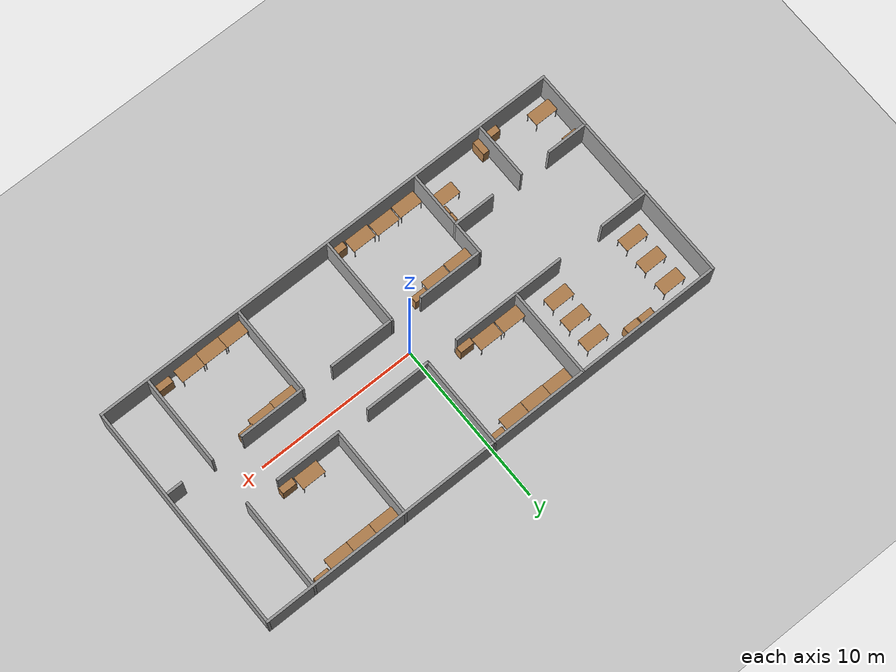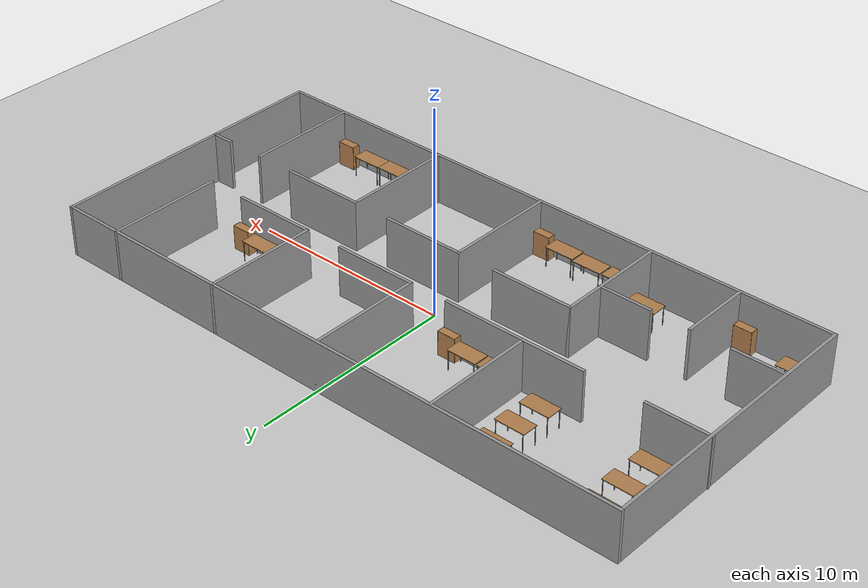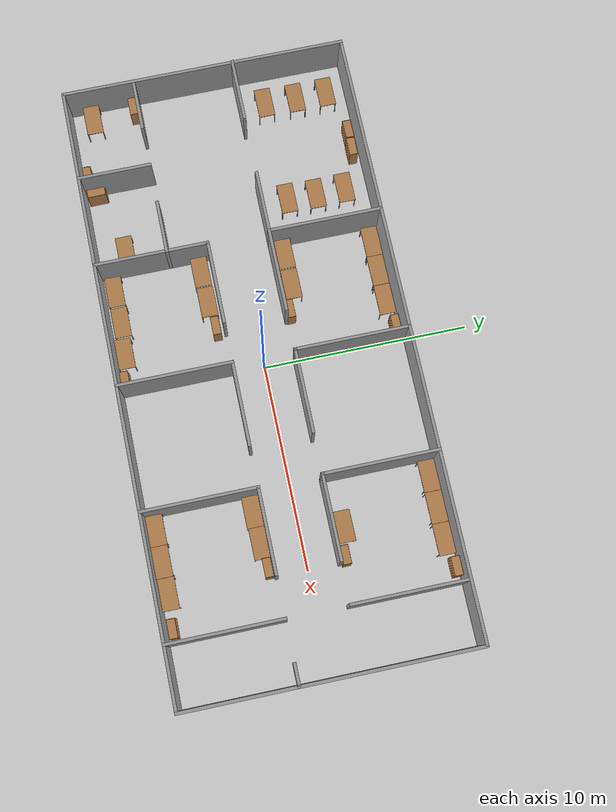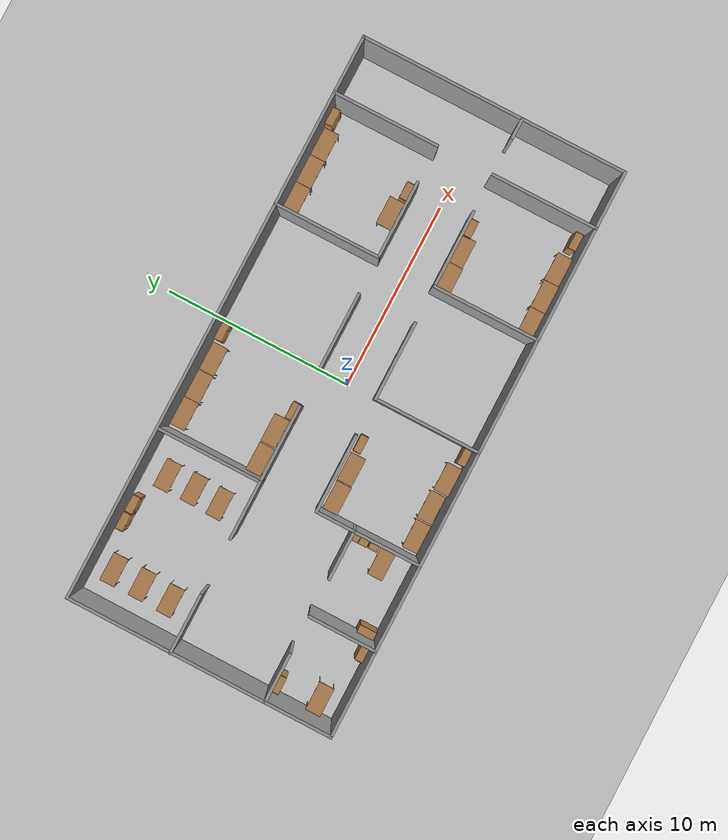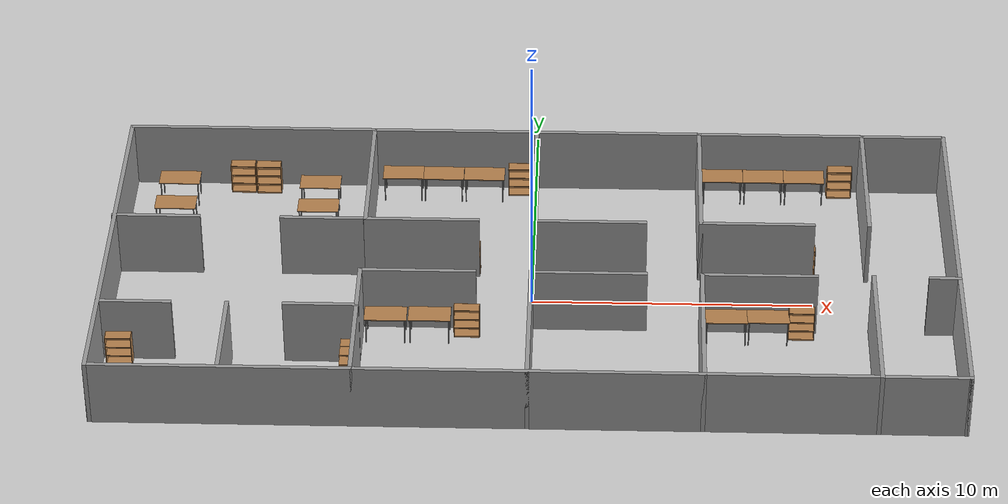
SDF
<sdf version="1.6">
 <world name="default">
  <light name="sun" type="directional">
   <pose>0 0 10 0 -0 0</pose>
   <diffuse>0.8 0.8 0.8 1</diffuse>
   <specular>0.2 0.2 0.2 1</specular>
   <attenuation>
    <range>1000</range>
    <constant>0.9</constant>
    <linear>0.01</linear>
    <quadratic>0.001</quadratic>
   </attenuation>
   <direction>-0.5 0.1 -0.9</direction>
  </light>
  <model name="ground_plane">
   <static>1</static>
   <link name="link">
    <collision name="collision">
     <geometry><plane><normal>0 0 1</normal><size>100 100</size></plane></geometry>
     <surface>
      <contact><collide_bitmask>65535</collide_bitmask></contact>
      <friction><ode><mu>100</mu><mu2>50</mu2></ode></friction>
     </surface>
    </collision>
    <visual name="visual">
     <cast_shadows>0</cast_shadows>
     <geometry><plane><normal>0 0 1</normal><size>100 100</size></plane></geometry>
     <material>
      <script><uri>file://media/materials/scripts/gazebo.material</uri><name>Gazebo/Grey</name></script>
     </material>
    </visual>
   </link>
  </model>
  <gravity>0 0 -9.8</gravity>
  <magnetic_field>6e-06 2.3e-05 -4.2e-05</magnetic_field>
  <atmosphere type="adiabatic"/>
  <physics name="default_physics" default="0" type="ode">
   <max_step_size>0.001</max_step_size>
   <real_time_factor>1</real_time_factor>
   <real_time_update_rate>1000</real_time_update_rate>
  </physics>
  <scene><ambient>0.4 0.4 0.4 1</ambient><background>0.7 0.7 0.7 1</background><shadows>1</shadows></scene>
  <audio><device>default</device></audio>
  <spherical_coordinates>
   <surface_model>EARTH_WGS84</surface_model>
   <latitude_deg>0</latitude_deg>
   <longitude_deg>0</longitude_deg>
   <elevation>0</elevation>
   <heading_deg>0</heading_deg>
  </spherical_coordinates>
  <model name="5th_floor3">
   <pose>-0.019 0 0 0 -0 0</pose>
   <link name="Wall_0">
    <collision name="Wall_0_Collision">
     <geometry><box><size>14.15 0.15 2.5</size></box></geometry>
     <pose>0 0 1.25 0 -0 0</pose>
    </collision>
    <visual name="Wall_0_Visual">
     <pose>0 0 1.25 0 -0 0</pose>
     <geometry><box><size>14.15 0.15 2.5</size></box></geometry>
     <material>
      <script><uri>file://media/materials/scripts/gazebo.material</uri><name>Gazebo/Grey</name></script>
      <ambient>1 1 1 1</ambient>
     </material>
     <meta><layer>0</layer></meta>
    </visual>
    <pose>-14.981 0 0 0 -0 -1.5708</pose>
   </link>
   <link name="Wall_1">
    <collision name="Wall_1_Collision">
     <geometry><box><size>30.15 0.15 2.5</size></box></geometry>
     <pose>0 0 1.25 0 -0 0</pose>
    </collision>
    <visual name="Wall_1_Visual">
     <pose>0 0 1.25 0 -0 0</pose>
     <geometry><box><size>30.15 0.15 2.5</size></box></geometry>
     <material>
      <script><uri>file://media/materials/scripts/gazebo.material</uri><name>Gazebo/Grey</name></script>
      <ambient>1 1 1 1</ambient>
     </material>
     <meta><layer>0</layer></meta>
    </visual>
    <pose>0.019 -7 0 0 -0 0</pose>
   </link>
   <link name="Wall_10">
    <collision name="Wall_10_Collision">
     <geometry><box><size>4.15 0.15 2.5</size></box></geometry>
     <pose>0 0 1.25 0 -0 0</pose>
    </collision>
    <visual name="Wall_10_Visual">
     <pose>0 0 1.25 0 -0 0</pose>
     <geometry><box><size>4.15 0.15 2.5</size></box></geometry>
     <material>
      <script><uri>file://media/materials/scripts/gazebo.material</uri><name>Gazebo/Grey</name></script>
      <ambient>1 1 1 1</ambient>
     </material>
     <meta><layer>0</layer></meta>
    </visual>
    <pose>-3.981 1.5 0 0 -0 0</pose>
   </link>
   <link name="Wall_12">
    <collision name="Wall_12_Collision">
     <geometry><box><size>5.65 0.15 2.5</size></box></geometry>
     <pose>0 0 1.25 0 -0 0</pose>
    </collision>
    <visual name="Wall_12_Visual">
     <pose>0 0 1.25 0 -0 0</pose>
     <geometry><box><size>5.65 0.15 2.5</size></box></geometry>
     <material>
      <script><uri>file://media/materials/scripts/gazebo.material</uri><name>Gazebo/Grey</name></script>
      <ambient>1 1 1 1</ambient>
     </material>
     <meta><layer>0</layer></meta>
    </visual>
    <pose>0.019 4.25 0 0 -0 -1.5708</pose>
   </link>
   <link name="Wall_13">
    <collision name="Wall_13_Collision">
     <geometry><box><size>0.15 0.15 2.5</size></box></geometry>
     <pose>0 0 1.25 0 -0 0</pose>
    </collision>
    <visual name="Wall_13_Visual">
     <pose>0 0 1.25 0 -0 0</pose>
     <geometry><box><size>0.15 0.15 2.5</size></box></geometry>
     <material>
      <script><uri>file://media/materials/scripts/gazebo.material</uri><name>Gazebo/Grey</name></script>
      <ambient>1 1 1 1</ambient>
     </material>
     <meta><layer>0</layer></meta>
    </visual>
    <pose>0.019 1.5 0 0 -0 0</pose>
   </link>
   <link name="Wall_14">
    <collision name="Wall_14_Collision">
     <geometry><box><size>4.15 0.15 2.5</size></box></geometry>
     <pose>0 0 1.25 0 -0 0</pose>
    </collision>
    <visual name="Wall_14_Visual">
     <pose>0 0 1.25 0 -0 0</pose>
     <geometry><box><size>4.15 0.15 2.5</size></box></geometry>
     <material>
      <script><uri>file://media/materials/scripts/gazebo.material</uri><name>Gazebo/Grey</name></script>
      <ambient>1 1 1 1</ambient>
     </material>
     <meta><layer>0</layer></meta>
    </visual>
    <pose>2.019 1.5 0 0 -0 0</pose>
   </link>
   <link name="Wall_16">
    <collision name="Wall_16_Collision">
     <geometry><box><size>5.65 0.15 2.5</size></box></geometry>
     <pose>0 0 1.25 0 -0 0</pose>
    </collision>
    <visual name="Wall_16_Visual">
     <pose>0 0 1.25 0 -0 0</pose>
     <geometry><box><size>5.65 0.15 2.5</size></box></geometry>
     <material>
      <script><uri>file://media/materials/scripts/gazebo.material</uri><name>Gazebo/Grey</name></script>
      <ambient>1 1 1 1</ambient>
     </material>
     <meta><layer>0</layer></meta>
    </visual>
    <pose>6.019 4.25 0 0 -0 -1.5708</pose>
   </link>
   <link name="Wall_17">
    <collision name="Wall_17_Collision">
     <geometry><box><size>4.15 0.15 2.5</size></box></geometry>
     <pose>0 0 1.25 0 -0 0</pose>
    </collision>
    <visual name="Wall_17_Visual">
     <pose>0 0 1.25 0 -0 0</pose>
     <geometry><box><size>4.15 0.15 2.5</size></box></geometry>
     <material>
      <script><uri>file://media/materials/scripts/gazebo.material</uri><name>Gazebo/Grey</name></script>
      <ambient>1 1 1 1</ambient>
     </material>
     <meta><layer>0</layer></meta>
    </visual>
    <pose>8.019 1.5 0 0 -0 0</pose>
   </link>
   <link name="Wall_2">
    <collision name="Wall_2_Collision">
     <geometry><box><size>14.15 0.15 2.5</size></box></geometry>
     <pose>0 0 1.25 0 -0 0</pose>
    </collision>
    <visual name="Wall_2_Visual">
     <pose>0 0 1.25 0 -0 0</pose>
     <geometry><box><size>14.15 0.15 2.5</size></box></geometry>
     <material>
      <script><uri>file://media/materials/scripts/gazebo.material</uri><name>Gazebo/Grey</name></script>
      <ambient>1 1 1 1</ambient>
     </material>
     <meta><layer>0</layer></meta>
    </visual>
    <pose>15.019 0 0 0 -0 1.5708</pose>
   </link>
   <link name="Wall_20">
    <collision name="Wall_20_Collision">
     <geometry><box><size>5.65 0.15 2.5</size></box></geometry>
     <pose>0 0 1.25 0 -0 0</pose>
    </collision>
    <visual name="Wall_20_Visual">
     <pose>0 0 1.25 0 -0 0</pose>
     <geometry><box><size>5.65 0.15 2.5</size></box></geometry>
     <material>
      <script><uri>file://media/materials/scripts/gazebo.material</uri><name>Gazebo/Grey</name></script>
      <ambient>1 1 1 1</ambient>
     </material>
     <meta><layer>0</layer></meta>
    </visual>
    <pose>12.019 4.25 0 0 -0 1.5708</pose>
   </link>
   <link name="Wall_22">
    <collision name="Wall_22_Collision">
     <geometry><box><size>2.65 0.15 2.5</size></box></geometry>
     <pose>0 0 1.25 0 -0 0</pose>
    </collision>
    <visual name="Wall_22_Visual">
     <pose>0 0 1.25 0 -0 0</pose>
     <geometry><box><size>2.65 0.15 2.5</size></box></geometry>
     <material>
      <script><uri>file://media/materials/scripts/gazebo.material</uri><name>Gazebo/Grey</name></script>
      <ambient>1 1 1 1</ambient>
     </material>
     <meta><layer>0</layer></meta>
    </visual>
    <pose>-13.731 -3.5 0 0 -0 0</pose>
   </link>
   <link name="Wall_24">
    <collision name="Wall_24_Collision">
     <geometry><box><size>3.65 0.15 2.5</size></box></geometry>
     <pose>0 0 1.25 0 -0 0</pose>
    </collision>
    <visual name="Wall_24_Visual">
     <pose>0 0 1.25 0 -0 0</pose>
     <geometry><box><size>3.65 0.15 2.5</size></box></geometry>
     <material>
      <script><uri>file://media/materials/scripts/gazebo.material</uri><name>Gazebo/Grey</name></script>
      <ambient>1 1 1 1</ambient>
     </material>
     <meta><layer>0</layer></meta>
    </visual>
    <pose>-10.481 -5.25 0 0 -0 -1.5708</pose>
   </link>
   <link name="Wall_26">
    <collision name="Wall_26_Collision">
     <geometry><box><size>2.65 0.15 2.5</size></box></geometry>
     <pose>0 0 1.25 0 -0 0</pose>
    </collision>
    <visual name="Wall_26_Visual">
     <pose>0 0 1.25 0 -0 0</pose>
     <geometry><box><size>2.65 0.15 2.5</size></box></geometry>
     <material>
      <script><uri>file://media/materials/scripts/gazebo.material</uri><name>Gazebo/Grey</name></script>
      <ambient>1 1 1 1</ambient>
     </material>
     <meta><layer>0</layer></meta>
    </visual>
    <pose>-7.231 -3.5 0 0 -0 0</pose>
   </link>
   <link name="Wall_28">
    <collision name="Wall_28_Collision">
     <geometry><box><size>5.65 0.15 2.5</size></box></geometry>
     <pose>0 0 1.25 0 -0 0</pose>
    </collision>
    <visual name="Wall_28_Visual">
     <pose>0 0 1.25 0 -0 0</pose>
     <geometry><box><size>5.65 0.15 2.5</size></box></geometry>
     <material>
      <script><uri>file://media/materials/scripts/gazebo.material</uri><name>Gazebo/Grey</name></script>
      <ambient>1 1 1 1</ambient>
     </material>
     <meta><layer>0</layer></meta>
    </visual>
    <pose>-5.981 -4.25 0 0 -0 1.5708</pose>
   </link>
   <link name="Wall_29">
    <collision name="Wall_29_Collision">
     <geometry><box><size>4.15 0.15 2.5</size></box></geometry>
     <pose>0 0 1.25 0 -0 0</pose>
    </collision>
    <visual name="Wall_29_Visual">
     <pose>0 0 1.25 0 -0 0</pose>
     <geometry><box><size>4.15 0.15 2.5</size></box></geometry>
     <material>
      <script><uri>file://media/materials/scripts/gazebo.material</uri><name>Gazebo/Grey</name></script>
      <ambient>1 1 1 1</ambient>
     </material>
     <meta><layer>0</layer></meta>
    </visual>
    <pose>-3.981 -1.5 0 0 -0 0</pose>
   </link>
   <link name="Wall_3">
    <collision name="Wall_3_Collision">
     <geometry><box><size>30.15 0.15 2.5</size></box></geometry>
     <pose>0 0 1.25 0 -0 0</pose>
    </collision>
    <visual name="Wall_3_Visual">
     <pose>0 0 1.25 0 -0 0</pose>
     <geometry><box><size>30.15 0.15 2.5</size></box></geometry>
     <material>
      <script><uri>file://media/materials/scripts/gazebo.material</uri><name>Gazebo/Grey</name></script>
      <ambient>1 1 1 1</ambient>
     </material>
     <meta><layer>0</layer></meta>
    </visual>
    <pose>0.019 7 0 0 -0 3.14159</pose>
   </link>
   <link name="Wall_31">
    <collision name="Wall_31_Collision">
     <geometry><box><size>5.65 0.15 2.5</size></box></geometry>
     <pose>0 0 1.25 0 -0 0</pose>
    </collision>
    <visual name="Wall_31_Visual">
     <pose>0 0 1.25 0 -0 0</pose>
     <geometry><box><size>5.65 0.15 2.5</size></box></geometry>
     <material>
      <script><uri>file://media/materials/scripts/gazebo.material</uri><name>Gazebo/Grey</name></script>
      <ambient>1 1 1 1</ambient>
     </material>
     <meta><layer>0</layer></meta>
    </visual>
    <pose>0.019 -4.25 0 0 -0 1.5708</pose>
   </link>
   <link name="Wall_32">
    <collision name="Wall_32_Collision">
     <geometry><box><size>4.161 0.15 2.5</size></box></geometry>
     <pose>0 0 1.25 0 -0 0</pose>
    </collision>
    <visual name="Wall_32_Visual">
     <pose>0 0 1.25 0 -0 0</pose>
     <geometry><box><size>4.161 0.15 2.5</size></box></geometry>
     <material>
      <script><uri>file://media/materials/scripts/gazebo.material</uri><name>Gazebo/Grey</name></script>
      <ambient>1 1 1 1</ambient>
     </material>
     <meta><layer>0</layer></meta>
    </visual>
    <pose>2.0245 -1.5 0 0 -0 0</pose>
   </link>
   <link name="Wall_34">
    <collision name="Wall_34_Collision">
     <geometry><box><size>5.65 0.15 2.5</size></box></geometry>
     <pose>0 0 1.25 0 -0 0</pose>
    </collision>
    <visual name="Wall_34_Visual">
     <pose>0 0 1.25 0 -0 0</pose>
     <geometry><box><size>5.65 0.15 2.5</size></box></geometry>
     <material>
      <script><uri>file://media/materials/scripts/gazebo.material</uri><name>Gazebo/Grey</name></script>
      <ambient>1 1 1 1</ambient>
     </material>
     <meta><layer>0</layer></meta>
    </visual>
    <pose>6.019 -4.25 0 0 -0 1.5708</pose>
   </link>
   <link name="Wall_35">
    <collision name="Wall_35_Collision">
     <geometry><box><size>4.15 0.15 2.5</size></box></geometry>
     <pose>0 0 1.25 0 -0 0</pose>
    </collision>
    <visual name="Wall_35_Visual">
     <pose>0 0 1.25 0 -0 0</pose>
     <geometry><box><size>4.15 0.15 2.5</size></box></geometry>
     <material>
      <script><uri>file://media/materials/scripts/gazebo.material</uri><name>Gazebo/Grey</name></script>
      <ambient>1 1 1 1</ambient>
     </material>
     <meta><layer>0</layer></meta>
    </visual>
    <pose>8.019 -1.5 0 0 -0 0</pose>
   </link>
   <link name="Wall_37">
    <collision name="Wall_37_Collision">
     <geometry><box><size>5.65 0.15 2.5</size></box></geometry>
     <pose>0 0 1.25 0 -0 0</pose>
    </collision>
    <visual name="Wall_37_Visual">
     <pose>0 0 1.25 0 -0 0</pose>
     <geometry><box><size>5.65 0.15 2.5</size></box></geometry>
     <material>
      <script><uri>file://media/materials/scripts/gazebo.material</uri><name>Gazebo/Grey</name></script>
      <ambient>1 1 1 1</ambient>
     </material>
     <meta><layer>0</layer></meta>
    </visual>
    <pose>12.019 -4.25 0 0 -0 -1.5708</pose>
   </link>
   <link name="Wall_39">
    <collision name="Wall_39_Collision">
     <geometry><box><size>1.15 0.15 2.5</size></box></geometry>
     <pose>0 0 1.25 0 -0 0</pose>
    </collision>
    <visual name="Wall_39_Visual">
     <pose>0 0 1.25 0 -0 0</pose>
     <geometry><box><size>1.15 0.15 2.5</size></box></geometry>
     <material>
      <script><uri>file://media/materials/scripts/gazebo.material</uri><name>Gazebo/Grey</name></script>
      <ambient>1 1 1 1</ambient>
     </material>
     <meta><layer>0</layer></meta>
    </visual>
    <pose>14.519 -1.5 0 0 -0 0</pose>
   </link>
   <link name="Wall_5">
    <collision name="Wall_5_Collision">
     <geometry><box><size>3.188 0.15 2.5</size></box></geometry>
     <pose>0 0 1.25 0 -0 0</pose>
    </collision>
    <visual name="Wall_5_Visual">
     <pose>0 0 1.25 0 -0 0</pose>
     <geometry><box><size>3.188 0.15 2.5</size></box></geometry>
     <material>
      <script><uri>file://media/materials/scripts/gazebo.material</uri><name>Gazebo/Grey</name></script>
      <ambient>1 1 1 1</ambient>
     </material>
     <meta><layer>0</layer></meta>
    </visual>
    <pose>-13.5 1.5 0 0 -0 0</pose>
   </link>
   <link name="Wall_7">
    <collision name="Wall_7_Collision">
     <geometry><box><size>3.15 0.15 2.5</size></box></geometry>
     <pose>0 0 1.25 0 -0 0</pose>
    </collision>
    <visual name="Wall_7_Visual">
     <pose>0 0 1.25 0 -0 0</pose>
     <geometry><box><size>3.15 0.15 2.5</size></box></geometry>
     <material>
      <script><uri>file://media/materials/scripts/gazebo.material</uri><name>Gazebo/Grey</name></script>
      <ambient>1 1 1 1</ambient>
     </material>
     <meta><layer>0</layer></meta>
    </visual>
    <pose>-7.481 1.5 0 0 -0 0</pose>
   </link>
   <link name="Wall_8">
    <collision name="Wall_8_Collision">
     <geometry><box><size>5.65 0.15 2.5</size></box></geometry>
     <pose>0 0 1.25 0 -0 0</pose>
    </collision>
    <visual name="Wall_8_Visual">
     <pose>0 0 1.25 0 -0 0</pose>
     <geometry><box><size>5.65 0.15 2.5</size></box></geometry>
     <material>
      <script><uri>file://media/materials/scripts/gazebo.material</uri><name>Gazebo/Grey</name></script>
      <ambient>1 1 1 1</ambient>
     </material>
     <meta><layer>0</layer></meta>
    </visual>
    <pose>-5.981 4.25 0 0 -0 1.5708</pose>
   </link>
   <static>1</static>
  </model>
  <model name="5th_floor_3.1">
   <model name="bookshelf">
    <static>1</static>
    <link name="link">
     <inertial><mass>1</mass></inertial>
     <collision name="back">
      <pose>0 0.005 0.6 0 -0 0</pose>
      <geometry><box><size>0.9 0.01 1.2</size></box></geometry>
     </collision>
     <visual name="visual1">
      <pose>0 0.005 0.6 0 -0 0</pose>
      <geometry><box><size>0.9 0.01 1.2</size></box></geometry>
      <material>
       <script><uri>file://media/materials/scripts/gazebo.material</uri><name>Gazebo/Wood</name></script>
      </material>
     </visual>
     <collision name="left_side">
      <pose>0.45 -0.195 0.6 0 -0 0</pose>
      <geometry><box><size>0.02 0.4 1.2</size></box></geometry>
     </collision>
     <visual name="visual2">
      <pose>0.45 -0.195 0.6 0 -0 0</pose>
      <geometry><box><size>0.02 0.4 1.2</size></box></geometry>
      <material>
       <script><uri>file://media/materials/scripts/gazebo.material</uri><name>Gazebo/Wood</name></script>
      </material>
     </visual>
     <collision name="right_side">
      <pose>-0.45 -0.195 0.6 0 -0 0</pose>
      <geometry><box><size>0.02 0.4 1.2</size></box></geometry>
     </collision>
     <visual name="visual3">
      <pose>-0.45 -0.195 0.6 0 -0 0</pose>
      <geometry><box><size>0.02 0.4 1.2</size></box></geometry>
      <material>
       <script><uri>file://media/materials/scripts/gazebo.material</uri><name>Gazebo/Wood</name></script>
      </material>
     </visual>
     <collision name="bottom">
      <pose>0 -0.195 0.03 0 -0 0</pose>
      <geometry><box><size>0.88 0.4 0.06</size></box></geometry>
     </collision>
     <visual name="visual4">
      <pose>0 -0.195 0.03 0 -0 0</pose>
      <geometry><box><size>0.88 0.4 0.06</size></box></geometry>
      <material>
       <script><uri>file://media/materials/scripts/gazebo.material</uri><name>Gazebo/Wood</name></script>
      </material>
     </visual>
     <collision name="top">
      <pose>0 -0.195 1.19 0 -0 0</pose>
      <geometry><box><size>0.88 0.4 0.02</size></box></geometry>
     </collision>
     <visual name="visual5">
      <pose>0 -0.195 1.19 0 -0 0</pose>
      <geometry><box><size>0.88 0.4 0.02</size></box></geometry>
      <material>
       <script><uri>file://media/materials/scripts/gazebo.material</uri><name>Gazebo/Wood</name></script>
      </material>
     </visual>
     <collision name="low_shelf">
      <pose>0 -0.195 0.43 0 -0 0</pose>
      <geometry><box><size>0.88 0.4 0.02</size></box></geometry>
     </collision>
     <visual name="visual6">
      <pose>0 -0.195 0.43 0 -0 0</pose>
      <geometry><box><size>0.88 0.4 0.02</size></box></geometry>
      <material>
       <script><uri>file://media/materials/scripts/gazebo.material</uri><name>Gazebo/Wood</name></script>
      </material>
     </visual>
     <collision name="high_shelf">
      <pose>0 -0.195 0.8 0 -0 0</pose>
      <geometry><box><size>0.88 0.4 0.02</size></box></geometry>
     </collision>
     <visual name="visual7">
      <pose>0 -0.195 0.8 0 -0 0</pose>
      <geometry><box><size>0.88 0.4 0.02</size></box></geometry>
      <material>
       <script><uri>file://media/materials/scripts/gazebo.material</uri><name>Gazebo/Wood</name></script>
      </material>
     </visual>
    </link>
    <pose>2.38677 6.21708 0 0 -0 0</pose>
   </model>
   <model name="bookshelf_0">
    <static>1</static>
    <link name="link">
     <inertial><mass>1</mass></inertial>
     <collision name="back">
      <pose>0 0.005 0.6 0 -0 0</pose>
      <geometry><box><size>0.9 0.01 1.2</size></box></geometry>
     </collision>
     <visual name="visual1">
      <pose>0 0.005 0.6 0 -0 0</pose>
      <geometry><box><size>0.9 0.01 1.2</size></box></geometry>
      <material>
       <script><uri>file://media/materials/scripts/gazebo.material</uri><name>Gazebo/Wood</name></script>
      </material>
     </visual>
     <collision name="left_side">
      <pose>0.45 -0.195 0.6 0 -0 0</pose>
      <geometry><box><size>0.02 0.4 1.2</size></box></geometry>
     </collision>
     <visual name="visual2">
      <pose>0.45 -0.195 0.6 0 -0 0</pose>
      <geometry><box><size>0.02 0.4 1.2</size></box></geometry>
      <material>
       <script><uri>file://media/materials/scripts/gazebo.material</uri><name>Gazebo/Wood</name></script>
      </material>
     </visual>
     <collision name="right_side">
      <pose>-0.45 -0.195 0.6 0 -0 0</pose>
      <geometry><box><size>0.02 0.4 1.2</size></box></geometry>
     </collision>
     <visual name="visual3">
      <pose>-0.45 -0.195 0.6 0 -0 0</pose>
      <geometry><box><size>0.02 0.4 1.2</size></box></geometry>
      <material>
       <script><uri>file://media/materials/scripts/gazebo.material</uri><name>Gazebo/Wood</name></script>
      </material>
     </visual>
     <collision name="bottom">
      <pose>0 -0.195 0.03 0 -0 0</pose>
      <geometry><box><size>0.88 0.4 0.06</size></box></geometry>
     </collision>
     <visual name="visual4">
      <pose>0 -0.195 0.03 0 -0 0</pose>
      <geometry><box><size>0.88 0.4 0.06</size></box></geometry>
      <material>
       <script><uri>file://media/materials/scripts/gazebo.material</uri><name>Gazebo/Wood</name></script>
      </material>
     </visual>
     <collision name="top">
      <pose>0 -0.195 1.19 0 -0 0</pose>
      <geometry><box><size>0.88 0.4 0.02</size></box></geometry>
     </collision>
     <visual name="visual5">
      <pose>0 -0.195 1.19 0 -0 0</pose>
      <geometry><box><size>0.88 0.4 0.02</size></box></geometry>
      <material>
       <script><uri>file://media/materials/scripts/gazebo.material</uri><name>Gazebo/Wood</name></script>
      </material>
     </visual>
     <collision name="low_shelf">
      <pose>0 -0.195 0.43 0 -0 0</pose>
      <geometry><box><size>0.88 0.4 0.02</size></box></geometry>
     </collision>
     <visual name="visual6">
      <pose>0 -0.195 0.43 0 -0 0</pose>
      <geometry><box><size>0.88 0.4 0.02</size></box></geometry>
      <material>
       <script><uri>file://media/materials/scripts/gazebo.material</uri><name>Gazebo/Wood</name></script>
      </material>
     </visual>
     <collision name="high_shelf">
      <pose>0 -0.195 0.8 0 -0 0</pose>
      <geometry><box><size>0.88 0.4 0.02</size></box></geometry>
     </collision>
     <visual name="visual7">
      <pose>0 -0.195 0.8 0 -0 0</pose>
      <geometry><box><size>0.88 0.4 0.02</size></box></geometry>
      <material>
       <script><uri>file://media/materials/scripts/gazebo.material</uri><name>Gazebo/Wood</name></script>
      </material>
     </visual>
    </link>
    <pose>0.608123 1.3708 0 0 -0 0</pose>
   </model>
   <model name="bookshelf_1">
    <static>1</static>
    <link name="link">
     <inertial><mass>1</mass></inertial>
     <collision name="back">
      <pose>0 0.005 0.6 0 -0 0</pose>
      <geometry><box><size>0.9 0.01 1.2</size></box></geometry>
     </collision>
     <visual name="visual1">
      <pose>0 0.005 0.6 0 -0 0</pose>
      <geometry><box><size>0.9 0.01 1.2</size></box></geometry>
      <material>
       <script><uri>file://media/materials/scripts/gazebo.material</uri><name>Gazebo/Wood</name></script>
      </material>
     </visual>
     <collision name="left_side">
      <pose>0.45 -0.195 0.6 0 -0 0</pose>
      <geometry><box><size>0.02 0.4 1.2</size></box></geometry>
     </collision>
     <visual name="visual2">
      <pose>0.45 -0.195 0.6 0 -0 0</pose>
      <geometry><box><size>0.02 0.4 1.2</size></box></geometry>
      <material>
       <script><uri>file://media/materials/scripts/gazebo.material</uri><name>Gazebo/Wood</name></script>
      </material>
     </visual>
     <collision name="right_side">
      <pose>-0.45 -0.195 0.6 0 -0 0</pose>
      <geometry><box><size>0.02 0.4 1.2</size></box></geometry>
     </collision>
     <visual name="visual3">
      <pose>-0.45 -0.195 0.6 0 -0 0</pose>
      <geometry><box><size>0.02 0.4 1.2</size></box></geometry>
      <material>
       <script><uri>file://media/materials/scripts/gazebo.material</uri><name>Gazebo/Wood</name></script>
      </material>
     </visual>
     <collision name="bottom">
      <pose>0 -0.195 0.03 0 -0 0</pose>
      <geometry><box><size>0.88 0.4 0.06</size></box></geometry>
     </collision>
     <visual name="visual4">
      <pose>0 -0.195 0.03 0 -0 0</pose>
      <geometry><box><size>0.88 0.4 0.06</size></box></geometry>
      <material>
       <script><uri>file://media/materials/scripts/gazebo.material</uri><name>Gazebo/Wood</name></script>
      </material>
     </visual>
     <collision name="top">
      <pose>0 -0.195 1.19 0 -0 0</pose>
      <geometry><box><size>0.88 0.4 0.02</size></box></geometry>
     </collision>
     <visual name="visual5">
      <pose>0 -0.195 1.19 0 -0 0</pose>
      <geometry><box><size>0.88 0.4 0.02</size></box></geometry>
      <material>
       <script><uri>file://media/materials/scripts/gazebo.material</uri><name>Gazebo/Wood</name></script>
      </material>
     </visual>
     <collision name="low_shelf">
      <pose>0 -0.195 0.43 0 -0 0</pose>
      <geometry><box><size>0.88 0.4 0.02</size></box></geometry>
     </collision>
     <visual name="visual6">
      <pose>0 -0.195 0.43 0 -0 0</pose>
      <geometry><box><size>0.88 0.4 0.02</size></box></geometry>
      <material>
       <script><uri>file://media/materials/scripts/gazebo.material</uri><name>Gazebo/Wood</name></script>
      </material>
     </visual>
     <collision name="high_shelf">
      <pose>0 -0.195 0.8 0 -0 0</pose>
      <geometry><box><size>0.88 0.4 0.02</size></box></geometry>
     </collision>
     <visual name="visual7">
      <pose>0 -0.195 0.8 0 -0 0</pose>
      <geometry><box><size>0.88 0.4 0.02</size></box></geometry>
      <material>
       <script><uri>file://media/materials/scripts/gazebo.material</uri><name>Gazebo/Wood</name></script>
      </material>
     </visual>
    </link>
    <pose>2.49451 -7.05231 0 0 -0 0</pose>
   </model>
   <model name="table">
    <static>1</static>
    <link name="link">
     <collision name="surface">
      <pose>0 0 1 0 -0 0</pose>
      <geometry><box><size>1.5 0.8 0.03</size></box></geometry>
      <surface><friction><ode><mu>0.6</mu><mu2>0.6</mu2></ode></friction></surface>
     </collision>
     <visual name="visual1">
      <pose>0 0 1 0 -0 0</pose>
      <geometry><box><size>1.5 0.8 0.03</size></box></geometry>
      <material>
       <script><uri>file://media/materials/scripts/gazebo.material</uri><name>Gazebo/Wood</name></script>
      </material>
     </visual>
     <collision name="front_left_leg">
      <pose>0.68 0.38 0.5 0 -0 0</pose>
      <geometry><cylinder><radius>0.02</radius><length>1</length></cylinder></geometry>
     </collision>
     <visual name="front_left_leg">
      <pose>0.68 0.38 0.5 0 -0 0</pose>
      <geometry><cylinder><radius>0.02</radius><length>1</length></cylinder></geometry>
      <material>
       <script><uri>file://media/materials/scripts/gazebo.material</uri><name>Gazebo/Grey</name></script>
      </material>
     </visual>
     <collision name="front_right_leg">
      <pose>0.68 -0.38 0.5 0 -0 0</pose>
      <geometry><cylinder><radius>0.02</radius><length>1</length></cylinder></geometry>
     </collision>
     <visual name="front_right_leg">
      <pose>0.68 -0.38 0.5 0 -0 0</pose>
      <geometry><cylinder><radius>0.02</radius><length>1</length></cylinder></geometry>
      <material>
       <script><uri>file://media/materials/scripts/gazebo.material</uri><name>Gazebo/Grey</name></script>
      </material>
     </visual>
     <collision name="back_right_leg">
      <pose>-0.68 -0.38 0.5 0 -0 0</pose>
      <geometry><cylinder><radius>0.02</radius><length>1</length></cylinder></geometry>
     </collision>
     <visual name="back_right_leg">
      <pose>-0.68 -0.38 0.5 0 -0 0</pose>
      <geometry><cylinder><radius>0.02</radius><length>1</length></cylinder></geometry>
      <material>
       <script><uri>file://media/materials/scripts/gazebo.material</uri><name>Gazebo/Grey</name></script>
      </material>
     </visual>
     <collision name="back_left_leg">
      <pose>-0.68 0.38 0.5 0 -0 0</pose>
      <geometry><cylinder><radius>0.02</radius><length>1</length></cylinder></geometry>
     </collision>
     <visual name="back_left_leg">
      <pose>-0.68 0.38 0.5 0 -0 0</pose>
      <geometry><cylinder><radius>0.02</radius><length>1</length></cylinder></geometry>
      <material>
       <script><uri>file://media/materials/scripts/gazebo.material</uri><name>Gazebo/Grey</name></script>
      </material>
     </visual>
    </link>
    <pose>1.04651 5.78746 0 0 -0 0</pose>
   </model>
   <model name="table_0">
    <static>1</static>
    <link name="link">
     <collision name="surface">
      <pose>0 0 1 0 -0 0</pose>
      <geometry><box><size>1.5 0.8 0.03</size></box></geometry>
      <surface><friction><ode><mu>0.6</mu><mu2>0.6</mu2></ode></friction></surface>
     </collision>
     <visual name="visual1">
      <pose>0 0 1 0 -0 0</pose>
      <geometry><box><size>1.5 0.8 0.03</size></box></geometry>
      <material>
       <script><uri>file://media/materials/scripts/gazebo.material</uri><name>Gazebo/Wood</name></script>
      </material>
     </visual>
     <collision name="front_left_leg">
      <pose>0.68 0.38 0.5 0 -0 0</pose>
      <geometry><cylinder><radius>0.02</radius><length>1</length></cylinder></geometry>
     </collision>
     <visual name="front_left_leg">
      <pose>0.68 0.38 0.5 0 -0 0</pose>
      <geometry><cylinder><radius>0.02</radius><length>1</length></cylinder></geometry>
      <material>
       <script><uri>file://media/materials/scripts/gazebo.material</uri><name>Gazebo/Grey</name></script>
      </material>
     </visual>
     <collision name="front_right_leg">
      <pose>0.68 -0.38 0.5 0 -0 0</pose>
      <geometry><cylinder><radius>0.02</radius><length>1</length></cylinder></geometry>
     </collision>
     <visual name="front_right_leg">
      <pose>0.68 -0.38 0.5 0 -0 0</pose>
      <geometry><cylinder><radius>0.02</radius><length>1</length></cylinder></geometry>
      <material>
       <script><uri>file://media/materials/scripts/gazebo.material</uri><name>Gazebo/Grey</name></script>
      </material>
     </visual>
     <collision name="back_right_leg">
      <pose>-0.68 -0.38 0.5 0 -0 0</pose>
      <geometry><cylinder><radius>0.02</radius><length>1</length></cylinder></geometry>
     </collision>
     <visual name="back_right_leg">
      <pose>-0.68 -0.38 0.5 0 -0 0</pose>
      <geometry><cylinder><radius>0.02</radius><length>1</length></cylinder></geometry>
      <material>
       <script><uri>file://media/materials/scripts/gazebo.material</uri><name>Gazebo/Grey</name></script>
      </material>
     </visual>
     <collision name="back_left_leg">
      <pose>-0.68 0.38 0.5 0 -0 0</pose>
      <geometry><cylinder><radius>0.02</radius><length>1</length></cylinder></geometry>
     </collision>
     <visual name="back_left_leg">
      <pose>-0.68 0.38 0.5 0 -0 0</pose>
      <geometry><cylinder><radius>0.02</radius><length>1</length></cylinder></geometry>
      <material>
       <script><uri>file://media/materials/scripts/gazebo.material</uri><name>Gazebo/Grey</name></script>
      </material>
     </visual>
    </link>
    <pose>-0.465507 5.78746 0 0 -0 0</pose>
   </model>
   <model name="table_1">
    <static>1</static>
    <link name="link">
     <collision name="surface">
      <pose>0 0 1 0 -0 0</pose>
      <geometry><box><size>1.5 0.8 0.03</size></box></geometry>
      <surface><friction><ode><mu>0.6</mu><mu2>0.6</mu2></ode></friction></surface>
     </collision>
     <visual name="visual1">
      <pose>0 0 1 0 -0 0</pose>
      <geometry><box><size>1.5 0.8 0.03</size></box></geometry>
      <material>
       <script><uri>file://media/materials/scripts/gazebo.material</uri><name>Gazebo/Wood</name></script>
      </material>
     </visual>
     <collision name="front_left_leg">
      <pose>0.68 0.38 0.5 0 -0 0</pose>
      <geometry><cylinder><radius>0.02</radius><length>1</length></cylinder></geometry>
     </collision>
     <visual name="front_left_leg">
      <pose>0.68 0.38 0.5 0 -0 0</pose>
      <geometry><cylinder><radius>0.02</radius><length>1</length></cylinder></geometry>
      <material>
       <script><uri>file://media/materials/scripts/gazebo.material</uri><name>Gazebo/Grey</name></script>
      </material>
     </visual>
     <collision name="front_right_leg">
      <pose>0.68 -0.38 0.5 0 -0 0</pose>
      <geometry><cylinder><radius>0.02</radius><length>1</length></cylinder></geometry>
     </collision>
     <visual name="front_right_leg">
      <pose>0.68 -0.38 0.5 0 -0 0</pose>
      <geometry><cylinder><radius>0.02</radius><length>1</length></cylinder></geometry>
      <material>
       <script><uri>file://media/materials/scripts/gazebo.material</uri><name>Gazebo/Grey</name></script>
      </material>
     </visual>
     <collision name="back_right_leg">
      <pose>-0.68 -0.38 0.5 0 -0 0</pose>
      <geometry><cylinder><radius>0.02</radius><length>1</length></cylinder></geometry>
     </collision>
     <visual name="back_right_leg">
      <pose>-0.68 -0.38 0.5 0 -0 0</pose>
      <geometry><cylinder><radius>0.02</radius><length>1</length></cylinder></geometry>
      <material>
       <script><uri>file://media/materials/scripts/gazebo.material</uri><name>Gazebo/Grey</name></script>
      </material>
     </visual>
     <collision name="back_left_leg">
      <pose>-0.68 0.38 0.5 0 -0 0</pose>
      <geometry><cylinder><radius>0.02</radius><length>1</length></cylinder></geometry>
     </collision>
     <visual name="back_left_leg">
      <pose>-0.68 0.38 0.5 0 -0 0</pose>
      <geometry><cylinder><radius>0.02</radius><length>1</length></cylinder></geometry>
      <material>
       <script><uri>file://media/materials/scripts/gazebo.material</uri><name>Gazebo/Grey</name></script>
      </material>
     </visual>
    </link>
    <pose>-1.96039 5.80467 0 0 -0 0</pose>
   </model>
   <model name="table_2">
    <static>1</static>
    <link name="link">
     <collision name="surface">
      <pose>0 0 1 0 -0 0</pose>
      <geometry><box><size>1.5 0.8 0.03</size></box></geometry>
      <surface><friction><ode><mu>0.6</mu><mu2>0.6</mu2></ode></friction></surface>
     </collision>
     <visual name="visual1">
      <pose>0 0 1 0 -0 0</pose>
      <geometry><box><size>1.5 0.8 0.03</size></box></geometry>
      <material>
       <script><uri>file://media/materials/scripts/gazebo.material</uri><name>Gazebo/Wood</name></script>
      </material>
     </visual>
     <collision name="front_left_leg">
      <pose>0.68 0.38 0.5 0 -0 0</pose>
      <geometry><cylinder><radius>0.02</radius><length>1</length></cylinder></geometry>
     </collision>
     <visual name="front_left_leg">
      <pose>0.68 0.38 0.5 0 -0 0</pose>
      <geometry><cylinder><radius>0.02</radius><length>1</length></cylinder></geometry>
      <material>
       <script><uri>file://media/materials/scripts/gazebo.material</uri><name>Gazebo/Grey</name></script>
      </material>
     </visual>
     <collision name="front_right_leg">
      <pose>0.68 -0.38 0.5 0 -0 0</pose>
      <geometry><cylinder><radius>0.02</radius><length>1</length></cylinder></geometry>
     </collision>
     <visual name="front_right_leg">
      <pose>0.68 -0.38 0.5 0 -0 0</pose>
      <geometry><cylinder><radius>0.02</radius><length>1</length></cylinder></geometry>
      <material>
       <script><uri>file://media/materials/scripts/gazebo.material</uri><name>Gazebo/Grey</name></script>
      </material>
     </visual>
     <collision name="back_right_leg">
      <pose>-0.68 -0.38 0.5 0 -0 0</pose>
      <geometry><cylinder><radius>0.02</radius><length>1</length></cylinder></geometry>
     </collision>
     <visual name="back_right_leg">
      <pose>-0.68 -0.38 0.5 0 -0 0</pose>
      <geometry><cylinder><radius>0.02</radius><length>1</length></cylinder></geometry>
      <material>
       <script><uri>file://media/materials/scripts/gazebo.material</uri><name>Gazebo/Grey</name></script>
      </material>
     </visual>
     <collision name="back_left_leg">
      <pose>-0.68 0.38 0.5 0 -0 0</pose>
      <geometry><cylinder><radius>0.02</radius><length>1</length></cylinder></geometry>
     </collision>
     <visual name="back_left_leg">
      <pose>-0.68 0.38 0.5 0 -0 0</pose>
      <geometry><cylinder><radius>0.02</radius><length>1</length></cylinder></geometry>
      <material>
       <script><uri>file://media/materials/scripts/gazebo.material</uri><name>Gazebo/Grey</name></script>
      </material>
     </visual>
    </link>
    <pose>-2.20621 1.50975 0 0 -0 0</pose>
   </model>
   <model name="table_3">
    <static>1</static>
    <link name="link">
     <collision name="surface">
      <pose>0 0 1 0 -0 0</pose>
      <geometry><box><size>1.5 0.8 0.03</size></box></geometry>
      <surface><friction><ode><mu>0.6</mu><mu2>0.6</mu2></ode></friction></surface>
     </collision>
     <visual name="visual1">
      <pose>0 0 1 0 -0 0</pose>
      <geometry><box><size>1.5 0.8 0.03</size></box></geometry>
      <material>
       <script><uri>file://media/materials/scripts/gazebo.material</uri><name>Gazebo/Wood</name></script>
      </material>
     </visual>
     <collision name="front_left_leg">
      <pose>0.68 0.38 0.5 0 -0 0</pose>
      <geometry><cylinder><radius>0.02</radius><length>1</length></cylinder></geometry>
     </collision>
     <visual name="front_left_leg">
      <pose>0.68 0.38 0.5 0 -0 0</pose>
      <geometry><cylinder><radius>0.02</radius><length>1</length></cylinder></geometry>
      <material>
       <script><uri>file://media/materials/scripts/gazebo.material</uri><name>Gazebo/Grey</name></script>
      </material>
     </visual>
     <collision name="front_right_leg">
      <pose>0.68 -0.38 0.5 0 -0 0</pose>
      <geometry><cylinder><radius>0.02</radius><length>1</length></cylinder></geometry>
     </collision>
     <visual name="front_right_leg">
      <pose>0.68 -0.38 0.5 0 -0 0</pose>
      <geometry><cylinder><radius>0.02</radius><length>1</length></cylinder></geometry>
      <material>
       <script><uri>file://media/materials/scripts/gazebo.material</uri><name>Gazebo/Grey</name></script>
      </material>
     </visual>
     <collision name="back_right_leg">
      <pose>-0.68 -0.38 0.5 0 -0 0</pose>
      <geometry><cylinder><radius>0.02</radius><length>1</length></cylinder></geometry>
     </collision>
     <visual name="back_right_leg">
      <pose>-0.68 -0.38 0.5 0 -0 0</pose>
      <geometry><cylinder><radius>0.02</radius><length>1</length></cylinder></geometry>
      <material>
       <script><uri>file://media/materials/scripts/gazebo.material</uri><name>Gazebo/Grey</name></script>
      </material>
     </visual>
     <collision name="back_left_leg">
      <pose>-0.68 0.38 0.5 0 -0 0</pose>
      <geometry><cylinder><radius>0.02</radius><length>1</length></cylinder></geometry>
     </collision>
     <visual name="back_left_leg">
      <pose>-0.68 0.38 0.5 0 -0 0</pose>
      <geometry><cylinder><radius>0.02</radius><length>1</length></cylinder></geometry>
      <material>
       <script><uri>file://media/materials/scripts/gazebo.material</uri><name>Gazebo/Grey</name></script>
      </material>
     </visual>
    </link>
    <pose>-0.646188 1.50825 0 0 -0 0</pose>
   </model>
   <model name="table_4">
    <static>1</static>
    <link name="link">
     <collision name="surface">
      <pose>0 0 1 0 -0 0</pose>
      <geometry><box><size>1.5 0.8 0.03</size></box></geometry>
      <surface><friction><ode><mu>0.6</mu><mu2>0.6</mu2></ode></friction></surface>
     </collision>
     <visual name="visual1">
      <pose>0 0 1 0 -0 0</pose>
      <geometry><box><size>1.5 0.8 0.03</size></box></geometry>
      <material>
       <script><uri>file://media/materials/scripts/gazebo.material</uri><name>Gazebo/Wood</name></script>
      </material>
     </visual>
     <collision name="front_left_leg">
      <pose>0.68 0.38 0.5 0 -0 0</pose>
      <geometry><cylinder><radius>0.02</radius><length>1</length></cylinder></geometry>
     </collision>
     <visual name="front_left_leg">
      <pose>0.68 0.38 0.5 0 -0 0</pose>
      <geometry><cylinder><radius>0.02</radius><length>1</length></cylinder></geometry>
      <material>
       <script><uri>file://media/materials/scripts/gazebo.material</uri><name>Gazebo/Grey</name></script>
      </material>
     </visual>
     <collision name="front_right_leg">
      <pose>0.68 -0.38 0.5 0 -0 0</pose>
      <geometry><cylinder><radius>0.02</radius><length>1</length></cylinder></geometry>
     </collision>
     <visual name="front_right_leg">
      <pose>0.68 -0.38 0.5 0 -0 0</pose>
      <geometry><cylinder><radius>0.02</radius><length>1</length></cylinder></geometry>
      <material>
       <script><uri>file://media/materials/scripts/gazebo.material</uri><name>Gazebo/Grey</name></script>
      </material>
     </visual>
     <collision name="back_right_leg">
      <pose>-0.68 -0.38 0.5 0 -0 0</pose>
      <geometry><cylinder><radius>0.02</radius><length>1</length></cylinder></geometry>
     </collision>
     <visual name="back_right_leg">
      <pose>-0.68 -0.38 0.5 0 -0 0</pose>
      <geometry><cylinder><radius>0.02</radius><length>1</length></cylinder></geometry>
      <material>
       <script><uri>file://media/materials/scripts/gazebo.material</uri><name>Gazebo/Grey</name></script>
      </material>
     </visual>
     <collision name="back_left_leg">
      <pose>-0.68 0.38 0.5 0 -0 0</pose>
      <geometry><cylinder><radius>0.02</radius><length>1</length></cylinder></geometry>
     </collision>
     <visual name="back_left_leg">
      <pose>-0.68 0.38 0.5 0 -0 0</pose>
      <geometry><cylinder><radius>0.02</radius><length>1</length></cylinder></geometry>
      <material>
       <script><uri>file://media/materials/scripts/gazebo.material</uri><name>Gazebo/Grey</name></script>
      </material>
     </visual>
    </link>
    <pose>1.15304 -7.03166 0 0 -0 0</pose>
   </model>
   <model name="table_5">
    <static>1</static>
    <link name="link">
     <collision name="surface">
      <pose>0 0 1 0 -0 0</pose>
      <geometry><box><size>1.5 0.8 0.03</size></box></geometry>
      <surface><friction><ode><mu>0.6</mu><mu2>0.6</mu2></ode></friction></surface>
     </collision>
     <visual name="visual1">
      <pose>0 0 1 0 -0 0</pose>
      <geometry><box><size>1.5 0.8 0.03</size></box></geometry>
      <material>
       <script><uri>file://media/materials/scripts/gazebo.material</uri><name>Gazebo/Wood</name></script>
      </material>
     </visual>
     <collision name="front_left_leg">
      <pose>0.68 0.38 0.5 0 -0 0</pose>
      <geometry><cylinder><radius>0.02</radius><length>1</length></cylinder></geometry>
     </collision>
     <visual name="front_left_leg">
      <pose>0.68 0.38 0.5 0 -0 0</pose>
      <geometry><cylinder><radius>0.02</radius><length>1</length></cylinder></geometry>
      <material>
       <script><uri>file://media/materials/scripts/gazebo.material</uri><name>Gazebo/Grey</name></script>
      </material>
     </visual>
     <collision name="front_right_leg">
      <pose>0.68 -0.38 0.5 0 -0 0</pose>
      <geometry><cylinder><radius>0.02</radius><length>1</length></cylinder></geometry>
     </collision>
     <visual name="front_right_leg">
      <pose>0.68 -0.38 0.5 0 -0 0</pose>
      <geometry><cylinder><radius>0.02</radius><length>1</length></cylinder></geometry>
      <material>
       <script><uri>file://media/materials/scripts/gazebo.material</uri><name>Gazebo/Grey</name></script>
      </material>
     </visual>
     <collision name="back_right_leg">
      <pose>-0.68 -0.38 0.5 0 -0 0</pose>
      <geometry><cylinder><radius>0.02</radius><length>1</length></cylinder></geometry>
     </collision>
     <visual name="back_right_leg">
      <pose>-0.68 -0.38 0.5 0 -0 0</pose>
      <geometry><cylinder><radius>0.02</radius><length>1</length></cylinder></geometry>
      <material>
       <script><uri>file://media/materials/scripts/gazebo.material</uri><name>Gazebo/Grey</name></script>
      </material>
     </visual>
     <collision name="back_left_leg">
      <pose>-0.68 0.38 0.5 0 -0 0</pose>
      <geometry><cylinder><radius>0.02</radius><length>1</length></cylinder></geometry>
     </collision>
     <visual name="back_left_leg">
      <pose>-0.68 0.38 0.5 0 -0 0</pose>
      <geometry><cylinder><radius>0.02</radius><length>1</length></cylinder></geometry>
      <material>
       <script><uri>file://media/materials/scripts/gazebo.material</uri><name>Gazebo/Grey</name></script>
      </material>
     </visual>
    </link>
    <pose>-0.419243 -6.93921 0 0 -0 0</pose>
   </model>
   <model name="table_6">
    <static>1</static>
    <link name="link">
     <collision name="surface">
      <pose>0 0 1 0 -0 0</pose>
      <geometry><box><size>1.5 0.8 0.03</size></box></geometry>
      <surface><friction><ode><mu>0.6</mu><mu2>0.6</mu2></ode></friction></surface>
     </collision>
     <visual name="visual1">
      <pose>0 0 1 0 -0 0</pose>
      <geometry><box><size>1.5 0.8 0.03</size></box></geometry>
      <material>
       <script><uri>file://media/materials/scripts/gazebo.material</uri><name>Gazebo/Wood</name></script>
      </material>
     </visual>
     <collision name="front_left_leg">
      <pose>0.68 0.38 0.5 0 -0 0</pose>
      <geometry><cylinder><radius>0.02</radius><length>1</length></cylinder></geometry>
     </collision>
     <visual name="front_left_leg">
      <pose>0.68 0.38 0.5 0 -0 0</pose>
      <geometry><cylinder><radius>0.02</radius><length>1</length></cylinder></geometry>
      <material>
       <script><uri>file://media/materials/scripts/gazebo.material</uri><name>Gazebo/Grey</name></script>
      </material>
     </visual>
     <collision name="front_right_leg">
      <pose>0.68 -0.38 0.5 0 -0 0</pose>
      <geometry><cylinder><radius>0.02</radius><length>1</length></cylinder></geometry>
     </collision>
     <visual name="front_right_leg">
      <pose>0.68 -0.38 0.5 0 -0 0</pose>
      <geometry><cylinder><radius>0.02</radius><length>1</length></cylinder></geometry>
      <material>
       <script><uri>file://media/materials/scripts/gazebo.material</uri><name>Gazebo/Grey</name></script>
      </material>
     </visual>
     <collision name="back_right_leg">
      <pose>-0.68 -0.38 0.5 0 -0 0</pose>
      <geometry><cylinder><radius>0.02</radius><length>1</length></cylinder></geometry>
     </collision>
     <visual name="back_right_leg">
      <pose>-0.68 -0.38 0.5 0 -0 0</pose>
      <geometry><cylinder><radius>0.02</radius><length>1</length></cylinder></geometry>
      <material>
       <script><uri>file://media/materials/scripts/gazebo.material</uri><name>Gazebo/Grey</name></script>
      </material>
     </visual>
     <collision name="back_left_leg">
      <pose>-0.68 0.38 0.5 0 -0 0</pose>
      <geometry><cylinder><radius>0.02</radius><length>1</length></cylinder></geometry>
     </collision>
     <visual name="back_left_leg">
      <pose>-0.68 0.38 0.5 0 -0 0</pose>
      <geometry><cylinder><radius>0.02</radius><length>1</length></cylinder></geometry>
      <material>
       <script><uri>file://media/materials/scripts/gazebo.material</uri><name>Gazebo/Grey</name></script>
      </material>
     </visual>
    </link>
    <pose>-1.99142 -6.96227 0 0 -0 0</pose>
   </model>
   <static>0</static>
   <pose>-2.96973 0.578 0 0 -0 0</pose>
  </model>
  <model name="5th_floor_3.2">
   <model name="bookshelf">
    <static>1</static>
    <link name="link">
     <inertial><mass>1</mass></inertial>
     <collision name="back">
      <pose>0 0.005 0.6 0 -0 0</pose>
      <geometry><box><size>0.9 0.01 1.2</size></box></geometry>
     </collision>
     <visual name="visual1">
      <pose>0 0.005 0.6 0 -0 0</pose>
      <geometry><box><size>0.9 0.01 1.2</size></box></geometry>
      <material>
       <script><uri>file://media/materials/scripts/gazebo.material</uri><name>Gazebo/Wood</name></script>
      </material>
     </visual>
     <collision name="left_side">
      <pose>0.45 -0.195 0.6 0 -0 0</pose>
      <geometry><box><size>0.02 0.4 1.2</size></box></geometry>
     </collision>
     <visual name="visual2">
      <pose>0.45 -0.195 0.6 0 -0 0</pose>
      <geometry><box><size>0.02 0.4 1.2</size></box></geometry>
      <material>
       <script><uri>file://media/materials/scripts/gazebo.material</uri><name>Gazebo/Wood</name></script>
      </material>
     </visual>
     <collision name="right_side">
      <pose>-0.45 -0.195 0.6 0 -0 0</pose>
      <geometry><box><size>0.02 0.4 1.2</size></box></geometry>
     </collision>
     <visual name="visual3">
      <pose>-0.45 -0.195 0.6 0 -0 0</pose>
      <geometry><box><size>0.02 0.4 1.2</size></box></geometry>
      <material>
       <script><uri>file://media/materials/scripts/gazebo.material</uri><name>Gazebo/Wood</name></script>
      </material>
     </visual>
     <collision name="bottom">
      <pose>0 -0.195 0.03 0 -0 0</pose>
      <geometry><box><size>0.88 0.4 0.06</size></box></geometry>
     </collision>
     <visual name="visual4">
      <pose>0 -0.195 0.03 0 -0 0</pose>
      <geometry><box><size>0.88 0.4 0.06</size></box></geometry>
      <material>
       <script><uri>file://media/materials/scripts/gazebo.material</uri><name>Gazebo/Wood</name></script>
      </material>
     </visual>
     <collision name="top">
      <pose>0 -0.195 1.19 0 -0 0</pose>
      <geometry><box><size>0.88 0.4 0.02</size></box></geometry>
     </collision>
     <visual name="visual5">
      <pose>0 -0.195 1.19 0 -0 0</pose>
      <geometry><box><size>0.88 0.4 0.02</size></box></geometry>
      <material>
       <script><uri>file://media/materials/scripts/gazebo.material</uri><name>Gazebo/Wood</name></script>
      </material>
     </visual>
     <collision name="low_shelf">
      <pose>0 -0.195 0.43 0 -0 0</pose>
      <geometry><box><size>0.88 0.4 0.02</size></box></geometry>
     </collision>
     <visual name="visual6">
      <pose>0 -0.195 0.43 0 -0 0</pose>
      <geometry><box><size>0.88 0.4 0.02</size></box></geometry>
      <material>
       <script><uri>file://media/materials/scripts/gazebo.material</uri><name>Gazebo/Wood</name></script>
      </material>
     </visual>
     <collision name="high_shelf">
      <pose>0 -0.195 0.8 0 -0 0</pose>
      <geometry><box><size>0.88 0.4 0.02</size></box></geometry>
     </collision>
     <visual name="visual7">
      <pose>0 -0.195 0.8 0 -0 0</pose>
      <geometry><box><size>0.88 0.4 0.02</size></box></geometry>
      <material>
       <script><uri>file://media/materials/scripts/gazebo.material</uri><name>Gazebo/Wood</name></script>
      </material>
     </visual>
    </link>
    <pose>3.59774 2.10176 0 0 -0 0</pose>
   </model>
   <model name="bookshelf_0">
    <static>1</static>
    <link name="link">
     <inertial><mass>1</mass></inertial>
     <collision name="back">
      <pose>0 0.005 0.6 0 -0 0</pose>
      <geometry><box><size>0.9 0.01 1.2</size></box></geometry>
     </collision>
     <visual name="visual1">
      <pose>0 0.005 0.6 0 -0 0</pose>
      <geometry><box><size>0.9 0.01 1.2</size></box></geometry>
      <material>
       <script><uri>file://media/materials/scripts/gazebo.material</uri><name>Gazebo/Wood</name></script>
      </material>
     </visual>
     <collision name="left_side">
      <pose>0.45 -0.195 0.6 0 -0 0</pose>
      <geometry><box><size>0.02 0.4 1.2</size></box></geometry>
     </collision>
     <visual name="visual2">
      <pose>0.45 -0.195 0.6 0 -0 0</pose>
      <geometry><box><size>0.02 0.4 1.2</size></box></geometry>
      <material>
       <script><uri>file://media/materials/scripts/gazebo.material</uri><name>Gazebo/Wood</name></script>
      </material>
     </visual>
     <collision name="right_side">
      <pose>-0.45 -0.195 0.6 0 -0 0</pose>
      <geometry><box><size>0.02 0.4 1.2</size></box></geometry>
     </collision>
     <visual name="visual3">
      <pose>-0.45 -0.195 0.6 0 -0 0</pose>
      <geometry><box><size>0.02 0.4 1.2</size></box></geometry>
      <material>
       <script><uri>file://media/materials/scripts/gazebo.material</uri><name>Gazebo/Wood</name></script>
      </material>
     </visual>
     <collision name="bottom">
      <pose>0 -0.195 0.03 0 -0 0</pose>
      <geometry><box><size>0.88 0.4 0.06</size></box></geometry>
     </collision>
     <visual name="visual4">
      <pose>0 -0.195 0.03 0 -0 0</pose>
      <geometry><box><size>0.88 0.4 0.06</size></box></geometry>
      <material>
       <script><uri>file://media/materials/scripts/gazebo.material</uri><name>Gazebo/Wood</name></script>
      </material>
     </visual>
     <collision name="top">
      <pose>0 -0.195 1.19 0 -0 0</pose>
      <geometry><box><size>0.88 0.4 0.02</size></box></geometry>
     </collision>
     <visual name="visual5">
      <pose>0 -0.195 1.19 0 -0 0</pose>
      <geometry><box><size>0.88 0.4 0.02</size></box></geometry>
      <material>
       <script><uri>file://media/materials/scripts/gazebo.material</uri><name>Gazebo/Wood</name></script>
      </material>
     </visual>
     <collision name="low_shelf">
      <pose>0 -0.195 0.43 0 -0 0</pose>
      <geometry><box><size>0.88 0.4 0.02</size></box></geometry>
     </collision>
     <visual name="visual6">
      <pose>0 -0.195 0.43 0 -0 0</pose>
      <geometry><box><size>0.88 0.4 0.02</size></box></geometry>
      <material>
       <script><uri>file://media/materials/scripts/gazebo.material</uri><name>Gazebo/Wood</name></script>
      </material>
     </visual>
     <collision name="high_shelf">
      <pose>0 -0.195 0.8 0 -0 0</pose>
      <geometry><box><size>0.88 0.4 0.02</size></box></geometry>
     </collision>
     <visual name="visual7">
      <pose>0 -0.195 0.8 0 -0 0</pose>
      <geometry><box><size>0.88 0.4 0.02</size></box></geometry>
      <material>
       <script><uri>file://media/materials/scripts/gazebo.material</uri><name>Gazebo/Wood</name></script>
      </material>
     </visual>
    </link>
    <pose>-4.10703 -2.55567 0 0 0 -1.56663</pose>
   </model>
   <model name="cabinet">
    <static>1</static>
    <link name="cabinet_bottom_plate">
     <inertial>
      <pose>0 0 -1 0 -0 0</pose>
      <inertia><ixx>2.05</ixx><ixy>0</ixy><ixz>0</ixz><iyy>2.05</iyy><iyz>0</iyz><izz>2.05</izz></inertia>
      <mass>25</mass>
     </inertial>
     <collision name="cabinet_bottom_plate_geom">
      <pose>0 0 0.01 0 -0 0</pose>
      <geometry><box><size>0.45 0.45 0.02</size></box></geometry>
     </collision>
     <visual name="cabinet_bottom_plate_geom_visual">
      <pose>0 0 0.01 0 -0 0</pose>
      <geometry><box><size>0.45 0.45 0.02</size></box></geometry>
      <material>
       <script><uri>file://media/materials/scripts/gazebo.material</uri><name>Gazebo/Wood</name></script>
      </material>
     </visual>
     <collision name="cabinet_bottom_plate_geom_cabinet_back_plate">
      <pose>0.235 0 0.51 0 -0 0</pose>
      <geometry><box><size>0.02 0.45 1.02</size></box></geometry>
     </collision>
     <visual name="cabinet_bottom_plate_geom_cabinet_back_plate_visual">
      <pose>0.235 0 0.51 0 -0 0</pose>
      <geometry><box><size>0.02 0.45 1.02</size></box></geometry>
      <material>
       <script><uri>file://media/materials/scripts/gazebo.material</uri><name>Gazebo/Wood</name></script>
      </material>
     </visual>
     <collision name="cabinet_bottom_plate_geom_cabinet_left_plate">
      <pose>0 0.235 0.51 0 -0 0</pose>
      <geometry><box><size>0.45 0.02 1.02</size></box></geometry>
     </collision>
     <visual name="cabinet_bottom_plate_geom_cabinet_left_plate_visual">
      <pose>0 0.235 0.51 0 -0 0</pose>
      <geometry><box><size>0.45 0.02 1.02</size></box></geometry>
      <material>
       <script><uri>file://media/materials/scripts/gazebo.material</uri><name>Gazebo/Wood</name></script>
      </material>
     </visual>
     <collision name="cabinet_bottom_plate_geom_cabinet_middle_plate">
      <pose>0 0 0.51 0 -0 0</pose>
      <geometry><box><size>0.45 0.45 0.02</size></box></geometry>
     </collision>
     <visual name="cabinet_bottom_plate_geom_cabinet_middle_plate_visual">
      <pose>0 0 0.51 0 -0 0</pose>
      <geometry><box><size>0.45 0.45 0.02</size></box></geometry>
      <material>
       <script><uri>file://media/materials/scripts/gazebo.material</uri><name>Gazebo/Wood</name></script>
      </material>
     </visual>
     <collision name="cabinet_bottom_plate_geom_cabinet_right_plate">
      <pose>0 -0.235 0.51 0 -0 0</pose>
      <geometry><box><size>0.45 0.02 1.02</size></box></geometry>
     </collision>
     <visual name="cabinet_bottom_plate_geom_cabinet_right_plate_visual">
      <pose>0 -0.235 0.51 0 -0 0</pose>
      <geometry><box><size>0.45 0.02 1.02</size></box></geometry>
      <material>
       <script><uri>file://media/materials/scripts/gazebo.material</uri><name>Gazebo/Wood</name></script>
      </material>
     </visual>
     <collision name="cabinet_bottom_plate_geom_cabinet_top_plate">
      <pose>0 0 1.01 0 -0 0</pose>
      <geometry><box><size>0.45 0.45 0.02</size></box></geometry>
     </collision>
     <visual name="cabinet_bottom_plate_geom_cabinet_top_plate_visual">
      <pose>0 0 1.01 0 -0 0</pose>
      <geometry><box><size>0.45 0.45 0.02</size></box></geometry>
      <material>
       <script><uri>file://media/materials/scripts/gazebo.material</uri><name>Gazebo/Wood</name></script>
      </material>
     </visual>
    </link>
    <pose>-0.500512 0.057126 0 0 -0 0</pose>
   </model>
   <model name="cabinet_0">
    <static>1</static>
    <link name="cabinet_bottom_plate">
     <inertial>
      <pose>0 0 -1 0 -0 0</pose>
      <inertia><ixx>2.05</ixx><ixy>0</ixy><ixz>0</ixz><iyy>2.05</iyy><iyz>0</iyz><izz>2.05</izz></inertia>
      <mass>25</mass>
     </inertial>
     <collision name="cabinet_bottom_plate_geom">
      <pose>0 0 0.01 0 -0 0</pose>
      <geometry><box><size>0.45 0.45 0.02</size></box></geometry>
     </collision>
     <visual name="cabinet_bottom_plate_geom_visual">
      <pose>0 0 0.01 0 -0 0</pose>
      <geometry><box><size>0.45 0.45 0.02</size></box></geometry>
      <material>
       <script><uri>file://media/materials/scripts/gazebo.material</uri><name>Gazebo/Wood</name></script>
      </material>
     </visual>
     <collision name="cabinet_bottom_plate_geom_cabinet_back_plate">
      <pose>0.235 0 0.51 0 -0 0</pose>
      <geometry><box><size>0.02 0.45 1.02</size></box></geometry>
     </collision>
     <visual name="cabinet_bottom_plate_geom_cabinet_back_plate_visual">
      <pose>0.235 0 0.51 0 -0 0</pose>
      <geometry><box><size>0.02 0.45 1.02</size></box></geometry>
      <material>
       <script><uri>file://media/materials/scripts/gazebo.material</uri><name>Gazebo/Wood</name></script>
      </material>
     </visual>
     <collision name="cabinet_bottom_plate_geom_cabinet_left_plate">
      <pose>0 0.235 0.51 0 -0 0</pose>
      <geometry><box><size>0.45 0.02 1.02</size></box></geometry>
     </collision>
     <visual name="cabinet_bottom_plate_geom_cabinet_left_plate_visual">
      <pose>0 0.235 0.51 0 -0 0</pose>
      <geometry><box><size>0.45 0.02 1.02</size></box></geometry>
      <material>
       <script><uri>file://media/materials/scripts/gazebo.material</uri><name>Gazebo/Wood</name></script>
      </material>
     </visual>
     <collision name="cabinet_bottom_plate_geom_cabinet_middle_plate">
      <pose>0 0 0.51 0 -0 0</pose>
      <geometry><box><size>0.45 0.45 0.02</size></box></geometry>
     </collision>
     <visual name="cabinet_bottom_plate_geom_cabinet_middle_plate_visual">
      <pose>0 0 0.51 0 -0 0</pose>
      <geometry><box><size>0.45 0.45 0.02</size></box></geometry>
      <material>
       <script><uri>file://media/materials/scripts/gazebo.material</uri><name>Gazebo/Wood</name></script>
      </material>
     </visual>
     <collision name="cabinet_bottom_plate_geom_cabinet_right_plate">
      <pose>0 -0.235 0.51 0 -0 0</pose>
      <geometry><box><size>0.45 0.02 1.02</size></box></geometry>
     </collision>
     <visual name="cabinet_bottom_plate_geom_cabinet_right_plate_visual">
      <pose>0 -0.235 0.51 0 -0 0</pose>
      <geometry><box><size>0.45 0.02 1.02</size></box></geometry>
      <material>
       <script><uri>file://media/materials/scripts/gazebo.material</uri><name>Gazebo/Wood</name></script>
      </material>
     </visual>
     <collision name="cabinet_bottom_plate_geom_cabinet_top_plate">
      <pose>0 0 1.01 0 -0 0</pose>
      <geometry><box><size>0.45 0.45 0.02</size></box></geometry>
     </collision>
     <visual name="cabinet_bottom_plate_geom_cabinet_top_plate_visual">
      <pose>0 0 1.01 0 -0 0</pose>
      <geometry><box><size>0.45 0.45 0.02</size></box></geometry>
      <material>
       <script><uri>file://media/materials/scripts/gazebo.material</uri><name>Gazebo/Wood</name></script>
      </material>
     </visual>
    </link>
    <pose>-0.500512 -0.428354 0 0 -0 0</pose>
   </model>
   <model name="cabinet_1">
    <static>1</static>
    <link name="cabinet_bottom_plate">
     <inertial>
      <pose>0 0 -1 0 -0 0</pose>
      <inertia><ixx>2.05</ixx><ixy>0</ixy><ixz>0</ixz><iyy>2.05</iyy><iyz>0</iyz><izz>2.05</izz></inertia>
      <mass>25</mass>
     </inertial>
     <collision name="cabinet_bottom_plate_geom">
      <pose>0 0 0.01 0 -0 0</pose>
      <geometry><box><size>0.45 0.45 0.02</size></box></geometry>
     </collision>
     <visual name="cabinet_bottom_plate_geom_visual">
      <pose>0 0 0.01 0 -0 0</pose>
      <geometry><box><size>0.45 0.45 0.02</size></box></geometry>
      <material>
       <script><uri>file://media/materials/scripts/gazebo.material</uri><name>Gazebo/Wood</name></script>
      </material>
     </visual>
     <collision name="cabinet_bottom_plate_geom_cabinet_back_plate">
      <pose>0.235 0 0.51 0 -0 0</pose>
      <geometry><box><size>0.02 0.45 1.02</size></box></geometry>
     </collision>
     <visual name="cabinet_bottom_plate_geom_cabinet_back_plate_visual">
      <pose>0.235 0 0.51 0 -0 0</pose>
      <geometry><box><size>0.02 0.45 1.02</size></box></geometry>
      <material>
       <script><uri>file://media/materials/scripts/gazebo.material</uri><name>Gazebo/Wood</name></script>
      </material>
     </visual>
     <collision name="cabinet_bottom_plate_geom_cabinet_left_plate">
      <pose>0 0.235 0.51 0 -0 0</pose>
      <geometry><box><size>0.45 0.02 1.02</size></box></geometry>
     </collision>
     <visual name="cabinet_bottom_plate_geom_cabinet_left_plate_visual">
      <pose>0 0.235 0.51 0 -0 0</pose>
      <geometry><box><size>0.45 0.02 1.02</size></box></geometry>
      <material>
       <script><uri>file://media/materials/scripts/gazebo.material</uri><name>Gazebo/Wood</name></script>
      </material>
     </visual>
     <collision name="cabinet_bottom_plate_geom_cabinet_middle_plate">
      <pose>0 0 0.51 0 -0 0</pose>
      <geometry><box><size>0.45 0.45 0.02</size></box></geometry>
     </collision>
     <visual name="cabinet_bottom_plate_geom_cabinet_middle_plate_visual">
      <pose>0 0 0.51 0 -0 0</pose>
      <geometry><box><size>0.45 0.45 0.02</size></box></geometry>
      <material>
       <script><uri>file://media/materials/scripts/gazebo.material</uri><name>Gazebo/Wood</name></script>
      </material>
     </visual>
     <collision name="cabinet_bottom_plate_geom_cabinet_right_plate">
      <pose>0 -0.235 0.51 0 -0 0</pose>
      <geometry><box><size>0.45 0.02 1.02</size></box></geometry>
     </collision>
     <visual name="cabinet_bottom_plate_geom_cabinet_right_plate_visual">
      <pose>0 -0.235 0.51 0 -0 0</pose>
      <geometry><box><size>0.45 0.02 1.02</size></box></geometry>
      <material>
       <script><uri>file://media/materials/scripts/gazebo.material</uri><name>Gazebo/Wood</name></script>
      </material>
     </visual>
     <collision name="cabinet_bottom_plate_geom_cabinet_top_plate">
      <pose>0 0 1.01 0 -0 0</pose>
      <geometry><box><size>0.45 0.45 0.02</size></box></geometry>
     </collision>
     <visual name="cabinet_bottom_plate_geom_cabinet_top_plate_visual">
      <pose>0 0 1.01 0 -0 0</pose>
      <geometry><box><size>0.45 0.45 0.02</size></box></geometry>
      <material>
       <script><uri>file://media/materials/scripts/gazebo.material</uri><name>Gazebo/Wood</name></script>
      </material>
     </visual>
    </link>
    <pose>-0.47735 -0.960159 0 0 -0 0</pose>
   </model>
   <model name="table">
    <static>1</static>
    <link name="link">
     <collision name="surface">
      <pose>0 0 1 0 -0 0</pose>
      <geometry><box><size>1.5 0.8 0.03</size></box></geometry>
      <surface><friction><ode><mu>0.6</mu><mu2>0.6</mu2></ode></friction></surface>
     </collision>
     <visual name="visual1">
      <pose>0 0 1 0 -0 0</pose>
      <geometry><box><size>1.5 0.8 0.03</size></box></geometry>
      <material>
       <script><uri>file://media/materials/scripts/gazebo.material</uri><name>Gazebo/Wood</name></script>
      </material>
     </visual>
     <collision name="front_left_leg">
      <pose>0.68 0.38 0.5 0 -0 0</pose>
      <geometry><cylinder><radius>0.02</radius><length>1</length></cylinder></geometry>
     </collision>
     <visual name="front_left_leg">
      <pose>0.68 0.38 0.5 0 -0 0</pose>
      <geometry><cylinder><radius>0.02</radius><length>1</length></cylinder></geometry>
      <material>
       <script><uri>file://media/materials/scripts/gazebo.material</uri><name>Gazebo/Grey</name></script>
      </material>
     </visual>
     <collision name="front_right_leg">
      <pose>0.68 -0.38 0.5 0 -0 0</pose>
      <geometry><cylinder><radius>0.02</radius><length>1</length></cylinder></geometry>
     </collision>
     <visual name="front_right_leg">
      <pose>0.68 -0.38 0.5 0 -0 0</pose>
      <geometry><cylinder><radius>0.02</radius><length>1</length></cylinder></geometry>
      <material>
       <script><uri>file://media/materials/scripts/gazebo.material</uri><name>Gazebo/Grey</name></script>
      </material>
     </visual>
     <collision name="back_right_leg">
      <pose>-0.68 -0.38 0.5 0 -0 0</pose>
      <geometry><cylinder><radius>0.02</radius><length>1</length></cylinder></geometry>
     </collision>
     <visual name="back_right_leg">
      <pose>-0.68 -0.38 0.5 0 -0 0</pose>
      <geometry><cylinder><radius>0.02</radius><length>1</length></cylinder></geometry>
      <material>
       <script><uri>file://media/materials/scripts/gazebo.material</uri><name>Gazebo/Grey</name></script>
      </material>
     </visual>
     <collision name="back_left_leg">
      <pose>-0.68 0.38 0.5 0 -0 0</pose>
      <geometry><cylinder><radius>0.02</radius><length>1</length></cylinder></geometry>
     </collision>
     <visual name="back_left_leg">
      <pose>-0.68 0.38 0.5 0 -0 0</pose>
      <geometry><cylinder><radius>0.02</radius><length>1</length></cylinder></geometry>
      <material>
       <script><uri>file://media/materials/scripts/gazebo.material</uri><name>Gazebo/Grey</name></script>
      </material>
     </visual>
    </link>
    <pose>0.746904 1.71954 0 0 -0 0</pose>
   </model>
   <model name="table_0">
    <static>1</static>
    <link name="link">
     <collision name="surface">
      <pose>0 0 1 0 -0 0</pose>
      <geometry><box><size>1.5 0.8 0.03</size></box></geometry>
      <surface><friction><ode><mu>0.6</mu><mu2>0.6</mu2></ode></friction></surface>
     </collision>
     <visual name="visual1">
      <pose>0 0 1 0 -0 0</pose>
      <geometry><box><size>1.5 0.8 0.03</size></box></geometry>
      <material>
       <script><uri>file://media/materials/scripts/gazebo.material</uri><name>Gazebo/Wood</name></script>
      </material>
     </visual>
     <collision name="front_left_leg">
      <pose>0.68 0.38 0.5 0 -0 0</pose>
      <geometry><cylinder><radius>0.02</radius><length>1</length></cylinder></geometry>
     </collision>
     <visual name="front_left_leg">
      <pose>0.68 0.38 0.5 0 -0 0</pose>
      <geometry><cylinder><radius>0.02</radius><length>1</length></cylinder></geometry>
      <material>
       <script><uri>file://media/materials/scripts/gazebo.material</uri><name>Gazebo/Grey</name></script>
      </material>
     </visual>
     <collision name="front_right_leg">
      <pose>0.68 -0.38 0.5 0 -0 0</pose>
      <geometry><cylinder><radius>0.02</radius><length>1</length></cylinder></geometry>
     </collision>
     <visual name="front_right_leg">
      <pose>0.68 -0.38 0.5 0 -0 0</pose>
      <geometry><cylinder><radius>0.02</radius><length>1</length></cylinder></geometry>
      <material>
       <script><uri>file://media/materials/scripts/gazebo.material</uri><name>Gazebo/Grey</name></script>
      </material>
     </visual>
     <collision name="back_right_leg">
      <pose>-0.68 -0.38 0.5 0 -0 0</pose>
      <geometry><cylinder><radius>0.02</radius><length>1</length></cylinder></geometry>
     </collision>
     <visual name="back_right_leg">
      <pose>-0.68 -0.38 0.5 0 -0 0</pose>
      <geometry><cylinder><radius>0.02</radius><length>1</length></cylinder></geometry>
      <material>
       <script><uri>file://media/materials/scripts/gazebo.material</uri><name>Gazebo/Grey</name></script>
      </material>
     </visual>
     <collision name="back_left_leg">
      <pose>-0.68 0.38 0.5 0 -0 0</pose>
      <geometry><cylinder><radius>0.02</radius><length>1</length></cylinder></geometry>
     </collision>
     <visual name="back_left_leg">
      <pose>-0.68 0.38 0.5 0 -0 0</pose>
      <geometry><cylinder><radius>0.02</radius><length>1</length></cylinder></geometry>
      <material>
       <script><uri>file://media/materials/scripts/gazebo.material</uri><name>Gazebo/Grey</name></script>
      </material>
     </visual>
    </link>
    <pose>2.29592 1.7426 0 0 -0 0</pose>
   </model>
   <model name="table_1">
    <static>1</static>
    <link name="link">
     <collision name="surface">
      <pose>0 0 1 0 -0 0</pose>
      <geometry><box><size>1.5 0.8 0.03</size></box></geometry>
      <surface><friction><ode><mu>0.6</mu><mu2>0.6</mu2></ode></friction></surface>
     </collision>
     <visual name="visual1">
      <pose>0 0 1 0 -0 0</pose>
      <geometry><box><size>1.5 0.8 0.03</size></box></geometry>
      <material>
       <script><uri>file://media/materials/scripts/gazebo.material</uri><name>Gazebo/Wood</name></script>
      </material>
     </visual>
     <collision name="front_left_leg">
      <pose>0.68 0.38 0.5 0 -0 0</pose>
      <geometry><cylinder><radius>0.02</radius><length>1</length></cylinder></geometry>
     </collision>
     <visual name="front_left_leg">
      <pose>0.68 0.38 0.5 0 -0 0</pose>
      <geometry><cylinder><radius>0.02</radius><length>1</length></cylinder></geometry>
      <material>
       <script><uri>file://media/materials/scripts/gazebo.material</uri><name>Gazebo/Grey</name></script>
      </material>
     </visual>
     <collision name="front_right_leg">
      <pose>0.68 -0.38 0.5 0 -0 0</pose>
      <geometry><cylinder><radius>0.02</radius><length>1</length></cylinder></geometry>
     </collision>
     <visual name="front_right_leg">
      <pose>0.68 -0.38 0.5 0 -0 0</pose>
      <geometry><cylinder><radius>0.02</radius><length>1</length></cylinder></geometry>
      <material>
       <script><uri>file://media/materials/scripts/gazebo.material</uri><name>Gazebo/Grey</name></script>
      </material>
     </visual>
     <collision name="back_right_leg">
      <pose>-0.68 -0.38 0.5 0 -0 0</pose>
      <geometry><cylinder><radius>0.02</radius><length>1</length></cylinder></geometry>
     </collision>
     <visual name="back_right_leg">
      <pose>-0.68 -0.38 0.5 0 -0 0</pose>
      <geometry><cylinder><radius>0.02</radius><length>1</length></cylinder></geometry>
      <material>
       <script><uri>file://media/materials/scripts/gazebo.material</uri><name>Gazebo/Grey</name></script>
      </material>
     </visual>
     <collision name="back_left_leg">
      <pose>-0.68 0.38 0.5 0 -0 0</pose>
      <geometry><cylinder><radius>0.02</radius><length>1</length></cylinder></geometry>
     </collision>
     <visual name="back_left_leg">
      <pose>-0.68 0.38 0.5 0 -0 0</pose>
      <geometry><cylinder><radius>0.02</radius><length>1</length></cylinder></geometry>
      <material>
       <script><uri>file://media/materials/scripts/gazebo.material</uri><name>Gazebo/Grey</name></script>
      </material>
     </visual>
    </link>
    <pose>-1.05517 -1.67685 0 0 -0 0</pose>
   </model>
   <static>0</static>
   <pose>-5.8522 -3.82308 0 0 -0 0</pose>
  </model>
  <model name="bookshelf_2">
   <static>1</static>
   <link name="link">
    <inertial><mass>1</mass></inertial>
    <collision name="back">
     <pose>0 0.005 0.6 0 -0 0</pose>
     <geometry><box><size>0.9 0.01 1.2</size></box></geometry>
    </collision>
    <visual name="visual1">
     <pose>0 0.005 0.6 0 -0 0</pose>
     <geometry><box><size>0.9 0.01 1.2</size></box></geometry>
     <material>
      <script><uri>file://media/materials/scripts/gazebo.material</uri><name>Gazebo/Wood</name></script>
     </material>
    </visual>
    <collision name="left_side">
     <pose>0.45 -0.195 0.6 0 -0 0</pose>
     <geometry><box><size>0.02 0.4 1.2</size></box></geometry>
    </collision>
    <visual name="visual2">
     <pose>0.45 -0.195 0.6 0 -0 0</pose>
     <geometry><box><size>0.02 0.4 1.2</size></box></geometry>
     <material>
      <script><uri>file://media/materials/scripts/gazebo.material</uri><name>Gazebo/Wood</name></script>
     </material>
    </visual>
    <collision name="right_side">
     <pose>-0.45 -0.195 0.6 0 -0 0</pose>
     <geometry><box><size>0.02 0.4 1.2</size></box></geometry>
    </collision>
    <visual name="visual3">
     <pose>-0.45 -0.195 0.6 0 -0 0</pose>
     <geometry><box><size>0.02 0.4 1.2</size></box></geometry>
     <material>
      <script><uri>file://media/materials/scripts/gazebo.material</uri><name>Gazebo/Wood</name></script>
     </material>
    </visual>
    <collision name="bottom">
     <pose>0 -0.195 0.03 0 -0 0</pose>
     <geometry><box><size>0.88 0.4 0.06</size></box></geometry>
    </collision>
    <visual name="visual4">
     <pose>0 -0.195 0.03 0 -0 0</pose>
     <geometry><box><size>0.88 0.4 0.06</size></box></geometry>
     <material>
      <script><uri>file://media/materials/scripts/gazebo.material</uri><name>Gazebo/Wood</name></script>
     </material>
    </visual>
    <collision name="top">
     <pose>0 -0.195 1.19 0 -0 0</pose>
     <geometry><box><size>0.88 0.4 0.02</size></box></geometry>
    </collision>
    <visual name="visual5">
     <pose>0 -0.195 1.19 0 -0 0</pose>
     <geometry><box><size>0.88 0.4 0.02</size></box></geometry>
     <material>
      <script><uri>file://media/materials/scripts/gazebo.material</uri><name>Gazebo/Wood</name></script>
     </material>
    </visual>
    <collision name="low_shelf">
     <pose>0 -0.195 0.43 0 -0 0</pose>
     <geometry><box><size>0.88 0.4 0.02</size></box></geometry>
    </collision>
    <visual name="visual6">
     <pose>0 -0.195 0.43 0 -0 0</pose>
     <geometry><box><size>0.88 0.4 0.02</size></box></geometry>
     <material>
      <script><uri>file://media/materials/scripts/gazebo.material</uri><name>Gazebo/Wood</name></script>
     </material>
    </visual>
    <collision name="high_shelf">
     <pose>0 -0.195 0.8 0 -0 0</pose>
     <geometry><box><size>0.88 0.4 0.02</size></box></geometry>
    </collision>
    <visual name="visual7">
     <pose>0 -0.195 0.8 0 -0 0</pose>
     <geometry><box><size>0.88 0.4 0.02</size></box></geometry>
     <material>
      <script><uri>file://media/materials/scripts/gazebo.material</uri><name>Gazebo/Wood</name></script>
     </material>
    </visual>
   </link>
   <pose>-9.95693 6.71493 0 0 -0 0</pose>
  </model>
  <model name="bookshelf_3">
   <static>1</static>
   <link name="link">
    <inertial><mass>1</mass></inertial>
    <collision name="back">
     <pose>0 0.005 0.6 0 -0 0</pose>
     <geometry><box><size>0.9 0.01 1.2</size></box></geometry>
    </collision>
    <visual name="visual1">
     <pose>0 0.005 0.6 0 -0 0</pose>
     <geometry><box><size>0.9 0.01 1.2</size></box></geometry>
     <material>
      <script><uri>file://media/materials/scripts/gazebo.material</uri><name>Gazebo/Wood</name></script>
     </material>
    </visual>
    <collision name="left_side">
     <pose>0.45 -0.195 0.6 0 -0 0</pose>
     <geometry><box><size>0.02 0.4 1.2</size></box></geometry>
    </collision>
    <visual name="visual2">
     <pose>0.45 -0.195 0.6 0 -0 0</pose>
     <geometry><box><size>0.02 0.4 1.2</size></box></geometry>
     <material>
      <script><uri>file://media/materials/scripts/gazebo.material</uri><name>Gazebo/Wood</name></script>
     </material>
    </visual>
    <collision name="right_side">
     <pose>-0.45 -0.195 0.6 0 -0 0</pose>
     <geometry><box><size>0.02 0.4 1.2</size></box></geometry>
    </collision>
    <visual name="visual3">
     <pose>-0.45 -0.195 0.6 0 -0 0</pose>
     <geometry><box><size>0.02 0.4 1.2</size></box></geometry>
     <material>
      <script><uri>file://media/materials/scripts/gazebo.material</uri><name>Gazebo/Wood</name></script>
     </material>
    </visual>
    <collision name="bottom">
     <pose>0 -0.195 0.03 0 -0 0</pose>
     <geometry><box><size>0.88 0.4 0.06</size></box></geometry>
    </collision>
    <visual name="visual4">
     <pose>0 -0.195 0.03 0 -0 0</pose>
     <geometry><box><size>0.88 0.4 0.06</size></box></geometry>
     <material>
      <script><uri>file://media/materials/scripts/gazebo.material</uri><name>Gazebo/Wood</name></script>
     </material>
    </visual>
    <collision name="top">
     <pose>0 -0.195 1.19 0 -0 0</pose>
     <geometry><box><size>0.88 0.4 0.02</size></box></geometry>
    </collision>
    <visual name="visual5">
     <pose>0 -0.195 1.19 0 -0 0</pose>
     <geometry><box><size>0.88 0.4 0.02</size></box></geometry>
     <material>
      <script><uri>file://media/materials/scripts/gazebo.material</uri><name>Gazebo/Wood</name></script>
     </material>
    </visual>
    <collision name="low_shelf">
     <pose>0 -0.195 0.43 0 -0 0</pose>
     <geometry><box><size>0.88 0.4 0.02</size></box></geometry>
    </collision>
    <visual name="visual6">
     <pose>0 -0.195 0.43 0 -0 0</pose>
     <geometry><box><size>0.88 0.4 0.02</size></box></geometry>
     <material>
      <script><uri>file://media/materials/scripts/gazebo.material</uri><name>Gazebo/Wood</name></script>
     </material>
    </visual>
    <collision name="high_shelf">
     <pose>0 -0.195 0.8 0 -0 0</pose>
     <geometry><box><size>0.88 0.4 0.02</size></box></geometry>
    </collision>
    <visual name="visual7">
     <pose>0 -0.195 0.8 0 -0 0</pose>
     <geometry><box><size>0.88 0.4 0.02</size></box></geometry>
     <material>
      <script><uri>file://media/materials/scripts/gazebo.material</uri><name>Gazebo/Wood</name></script>
     </material>
    </visual>
   </link>
   <pose>-10.9048 6.73806 0 0 -0 0</pose>
  </model>
  <model name="table_7">
   <static>1</static>
   <link name="link">
    <collision name="surface">
     <pose>0 0 1 0 -0 0</pose>
     <geometry><box><size>1.5 0.8 0.03</size></box></geometry>
     <surface><friction><ode><mu>0.6</mu><mu2>0.6</mu2></ode></friction></surface>
    </collision>
    <visual name="visual1">
     <pose>0 0 1 0 -0 0</pose>
     <geometry><box><size>1.5 0.8 0.03</size></box></geometry>
     <material>
      <script><uri>file://media/materials/scripts/gazebo.material</uri><name>Gazebo/Wood</name></script>
     </material>
    </visual>
    <collision name="front_left_leg">
     <pose>0.68 0.38 0.5 0 -0 0</pose>
     <geometry><cylinder><radius>0.02</radius><length>1</length></cylinder></geometry>
    </collision>
    <visual name="front_left_leg">
     <pose>0.68 0.38 0.5 0 -0 0</pose>
     <geometry><cylinder><radius>0.02</radius><length>1</length></cylinder></geometry>
     <material>
      <script><uri>file://media/materials/scripts/gazebo.material</uri><name>Gazebo/Grey</name></script>
     </material>
    </visual>
    <collision name="front_right_leg">
     <pose>0.68 -0.38 0.5 0 -0 0</pose>
     <geometry><cylinder><radius>0.02</radius><length>1</length></cylinder></geometry>
    </collision>
    <visual name="front_right_leg">
     <pose>0.68 -0.38 0.5 0 -0 0</pose>
     <geometry><cylinder><radius>0.02</radius><length>1</length></cylinder></geometry>
     <material>
      <script><uri>file://media/materials/scripts/gazebo.material</uri><name>Gazebo/Grey</name></script>
     </material>
    </visual>
    <collision name="back_right_leg">
     <pose>-0.68 -0.38 0.5 0 -0 0</pose>
     <geometry><cylinder><radius>0.02</radius><length>1</length></cylinder></geometry>
    </collision>
    <visual name="back_right_leg">
     <pose>-0.68 -0.38 0.5 0 -0 0</pose>
     <geometry><cylinder><radius>0.02</radius><length>1</length></cylinder></geometry>
     <material>
      <script><uri>file://media/materials/scripts/gazebo.material</uri><name>Gazebo/Grey</name></script>
     </material>
    </visual>
    <collision name="back_left_leg">
     <pose>-0.68 0.38 0.5 0 -0 0</pose>
     <geometry><cylinder><radius>0.02</radius><length>1</length></cylinder></geometry>
    </collision>
    <visual name="back_left_leg">
     <pose>-0.68 0.38 0.5 0 -0 0</pose>
     <geometry><cylinder><radius>0.02</radius><length>1</length></cylinder></geometry>
     <material>
      <script><uri>file://media/materials/scripts/gazebo.material</uri><name>Gazebo/Grey</name></script>
     </material>
    </visual>
   </link>
   <pose>-7.9682 5.69762 0 0 -0 0</pose>
  </model>
  <model name="table_8">
   <static>1</static>
   <link name="link">
    <collision name="surface">
     <pose>0 0 1 0 -0 0</pose>
     <geometry><box><size>1.5 0.8 0.03</size></box></geometry>
     <surface><friction><ode><mu>0.6</mu><mu2>0.6</mu2></ode></friction></surface>
    </collision>
    <visual name="visual1">
     <pose>0 0 1 0 -0 0</pose>
     <geometry><box><size>1.5 0.8 0.03</size></box></geometry>
     <material>
      <script><uri>file://media/materials/scripts/gazebo.material</uri><name>Gazebo/Wood</name></script>
     </material>
    </visual>
    <collision name="front_left_leg">
     <pose>0.68 0.38 0.5 0 -0 0</pose>
     <geometry><cylinder><radius>0.02</radius><length>1</length></cylinder></geometry>
    </collision>
    <visual name="front_left_leg">
     <pose>0.68 0.38 0.5 0 -0 0</pose>
     <geometry><cylinder><radius>0.02</radius><length>1</length></cylinder></geometry>
     <material>
      <script><uri>file://media/materials/scripts/gazebo.material</uri><name>Gazebo/Grey</name></script>
     </material>
    </visual>
    <collision name="front_right_leg">
     <pose>0.68 -0.38 0.5 0 -0 0</pose>
     <geometry><cylinder><radius>0.02</radius><length>1</length></cylinder></geometry>
    </collision>
    <visual name="front_right_leg">
     <pose>0.68 -0.38 0.5 0 -0 0</pose>
     <geometry><cylinder><radius>0.02</radius><length>1</length></cylinder></geometry>
     <material>
      <script><uri>file://media/materials/scripts/gazebo.material</uri><name>Gazebo/Grey</name></script>
     </material>
    </visual>
    <collision name="back_right_leg">
     <pose>-0.68 -0.38 0.5 0 -0 0</pose>
     <geometry><cylinder><radius>0.02</radius><length>1</length></cylinder></geometry>
    </collision>
    <visual name="back_right_leg">
     <pose>-0.68 -0.38 0.5 0 -0 0</pose>
     <geometry><cylinder><radius>0.02</radius><length>1</length></cylinder></geometry>
     <material>
      <script><uri>file://media/materials/scripts/gazebo.material</uri><name>Gazebo/Grey</name></script>
     </material>
    </visual>
    <collision name="back_left_leg">
     <pose>-0.68 0.38 0.5 0 -0 0</pose>
     <geometry><cylinder><radius>0.02</radius><length>1</length></cylinder></geometry>
    </collision>
    <visual name="back_left_leg">
     <pose>-0.68 0.38 0.5 0 -0 0</pose>
     <geometry><cylinder><radius>0.02</radius><length>1</length></cylinder></geometry>
     <material>
      <script><uri>file://media/materials/scripts/gazebo.material</uri><name>Gazebo/Grey</name></script>
     </material>
    </visual>
   </link>
   <pose>-7.94504 4.24099 0 0 -0 0</pose>
  </model>
  <model name="table_9">
   <static>1</static>
   <link name="link">
    <collision name="surface">
     <pose>0 0 1 0 -0 0</pose>
     <geometry><box><size>1.5 0.8 0.03</size></box></geometry>
     <surface><friction><ode><mu>0.6</mu><mu2>0.6</mu2></ode></friction></surface>
    </collision>
    <visual name="visual1">
     <pose>0 0 1 0 -0 0</pose>
     <geometry><box><size>1.5 0.8 0.03</size></box></geometry>
     <material>
      <script><uri>file://media/materials/scripts/gazebo.material</uri><name>Gazebo/Wood</name></script>
     </material>
    </visual>
    <collision name="front_left_leg">
     <pose>0.68 0.38 0.5 0 -0 0</pose>
     <geometry><cylinder><radius>0.02</radius><length>1</length></cylinder></geometry>
    </collision>
    <visual name="front_left_leg">
     <pose>0.68 0.38 0.5 0 -0 0</pose>
     <geometry><cylinder><radius>0.02</radius><length>1</length></cylinder></geometry>
     <material>
      <script><uri>file://media/materials/scripts/gazebo.material</uri><name>Gazebo/Grey</name></script>
     </material>
    </visual>
    <collision name="front_right_leg">
     <pose>0.68 -0.38 0.5 0 -0 0</pose>
     <geometry><cylinder><radius>0.02</radius><length>1</length></cylinder></geometry>
    </collision>
    <visual name="front_right_leg">
     <pose>0.68 -0.38 0.5 0 -0 0</pose>
     <geometry><cylinder><radius>0.02</radius><length>1</length></cylinder></geometry>
     <material>
      <script><uri>file://media/materials/scripts/gazebo.material</uri><name>Gazebo/Grey</name></script>
     </material>
    </visual>
    <collision name="back_right_leg">
     <pose>-0.68 -0.38 0.5 0 -0 0</pose>
     <geometry><cylinder><radius>0.02</radius><length>1</length></cylinder></geometry>
    </collision>
    <visual name="back_right_leg">
     <pose>-0.68 -0.38 0.5 0 -0 0</pose>
     <geometry><cylinder><radius>0.02</radius><length>1</length></cylinder></geometry>
     <material>
      <script><uri>file://media/materials/scripts/gazebo.material</uri><name>Gazebo/Grey</name></script>
     </material>
    </visual>
    <collision name="back_left_leg">
     <pose>-0.68 0.38 0.5 0 -0 0</pose>
     <geometry><cylinder><radius>0.02</radius><length>1</length></cylinder></geometry>
    </collision>
    <visual name="back_left_leg">
     <pose>-0.68 0.38 0.5 0 -0 0</pose>
     <geometry><cylinder><radius>0.02</radius><length>1</length></cylinder></geometry>
     <material>
      <script><uri>file://media/materials/scripts/gazebo.material</uri><name>Gazebo/Grey</name></script>
     </material>
    </visual>
   </link>
   <pose>-7.99136 2.80747 0 0 -0 0</pose>
  </model>
  <model name="table_10">
   <static>1</static>
   <link name="link">
    <collision name="surface">
     <pose>0 0 1 0 -0 0</pose>
     <geometry><box><size>1.5 0.8 0.03</size></box></geometry>
     <surface><friction><ode><mu>0.6</mu><mu2>0.6</mu2></ode></friction></surface>
    </collision>
    <visual name="visual1">
     <pose>0 0 1 0 -0 0</pose>
     <geometry><box><size>1.5 0.8 0.03</size></box></geometry>
     <material>
      <script><uri>file://media/materials/scripts/gazebo.material</uri><name>Gazebo/Wood</name></script>
     </material>
    </visual>
    <collision name="front_left_leg">
     <pose>0.68 0.38 0.5 0 -0 0</pose>
     <geometry><cylinder><radius>0.02</radius><length>1</length></cylinder></geometry>
    </collision>
    <visual name="front_left_leg">
     <pose>0.68 0.38 0.5 0 -0 0</pose>
     <geometry><cylinder><radius>0.02</radius><length>1</length></cylinder></geometry>
     <material>
      <script><uri>file://media/materials/scripts/gazebo.material</uri><name>Gazebo/Grey</name></script>
     </material>
    </visual>
    <collision name="front_right_leg">
     <pose>0.68 -0.38 0.5 0 -0 0</pose>
     <geometry><cylinder><radius>0.02</radius><length>1</length></cylinder></geometry>
    </collision>
    <visual name="front_right_leg">
     <pose>0.68 -0.38 0.5 0 -0 0</pose>
     <geometry><cylinder><radius>0.02</radius><length>1</length></cylinder></geometry>
     <material>
      <script><uri>file://media/materials/scripts/gazebo.material</uri><name>Gazebo/Grey</name></script>
     </material>
    </visual>
    <collision name="back_right_leg">
     <pose>-0.68 -0.38 0.5 0 -0 0</pose>
     <geometry><cylinder><radius>0.02</radius><length>1</length></cylinder></geometry>
    </collision>
    <visual name="back_right_leg">
     <pose>-0.68 -0.38 0.5 0 -0 0</pose>
     <geometry><cylinder><radius>0.02</radius><length>1</length></cylinder></geometry>
     <material>
      <script><uri>file://media/materials/scripts/gazebo.material</uri><name>Gazebo/Grey</name></script>
     </material>
    </visual>
    <collision name="back_left_leg">
     <pose>-0.68 0.38 0.5 0 -0 0</pose>
     <geometry><cylinder><radius>0.02</radius><length>1</length></cylinder></geometry>
    </collision>
    <visual name="back_left_leg">
     <pose>-0.68 0.38 0.5 0 -0 0</pose>
     <geometry><cylinder><radius>0.02</radius><length>1</length></cylinder></geometry>
     <material>
      <script><uri>file://media/materials/scripts/gazebo.material</uri><name>Gazebo/Grey</name></script>
     </material>
    </visual>
   </link>
   <pose>-13.1936 5.85945 0 0 -0 0</pose>
  </model>
  <model name="table_11">
   <static>1</static>
   <link name="link">
    <collision name="surface">
     <pose>0 0 1 0 -0 0</pose>
     <geometry><box><size>1.5 0.8 0.03</size></box></geometry>
     <surface><friction><ode><mu>0.6</mu><mu2>0.6</mu2></ode></friction></surface>
    </collision>
    <visual name="visual1">
     <pose>0 0 1 0 -0 0</pose>
     <geometry><box><size>1.5 0.8 0.03</size></box></geometry>
     <material>
      <script><uri>file://media/materials/scripts/gazebo.material</uri><name>Gazebo/Wood</name></script>
     </material>
    </visual>
    <collision name="front_left_leg">
     <pose>0.68 0.38 0.5 0 -0 0</pose>
     <geometry><cylinder><radius>0.02</radius><length>1</length></cylinder></geometry>
    </collision>
    <visual name="front_left_leg">
     <pose>0.68 0.38 0.5 0 -0 0</pose>
     <geometry><cylinder><radius>0.02</radius><length>1</length></cylinder></geometry>
     <material>
      <script><uri>file://media/materials/scripts/gazebo.material</uri><name>Gazebo/Grey</name></script>
     </material>
    </visual>
    <collision name="front_right_leg">
     <pose>0.68 -0.38 0.5 0 -0 0</pose>
     <geometry><cylinder><radius>0.02</radius><length>1</length></cylinder></geometry>
    </collision>
    <visual name="front_right_leg">
     <pose>0.68 -0.38 0.5 0 -0 0</pose>
     <geometry><cylinder><radius>0.02</radius><length>1</length></cylinder></geometry>
     <material>
      <script><uri>file://media/materials/scripts/gazebo.material</uri><name>Gazebo/Grey</name></script>
     </material>
    </visual>
    <collision name="back_right_leg">
     <pose>-0.68 -0.38 0.5 0 -0 0</pose>
     <geometry><cylinder><radius>0.02</radius><length>1</length></cylinder></geometry>
    </collision>
    <visual name="back_right_leg">
     <pose>-0.68 -0.38 0.5 0 -0 0</pose>
     <geometry><cylinder><radius>0.02</radius><length>1</length></cylinder></geometry>
     <material>
      <script><uri>file://media/materials/scripts/gazebo.material</uri><name>Gazebo/Grey</name></script>
     </material>
    </visual>
    <collision name="back_left_leg">
     <pose>-0.68 0.38 0.5 0 -0 0</pose>
     <geometry><cylinder><radius>0.02</radius><length>1</length></cylinder></geometry>
    </collision>
    <visual name="back_left_leg">
     <pose>-0.68 0.38 0.5 0 -0 0</pose>
     <geometry><cylinder><radius>0.02</radius><length>1</length></cylinder></geometry>
     <material>
      <script><uri>file://media/materials/scripts/gazebo.material</uri><name>Gazebo/Grey</name></script>
     </material>
    </visual>
   </link>
   <pose>-13.1936 4.31034 0 0 -0 0</pose>
  </model>
  <model name="table_12">
   <static>1</static>
   <link name="link">
    <collision name="surface">
     <pose>0 0 1 0 -0 0</pose>
     <geometry><box><size>1.5 0.8 0.03</size></box></geometry>
     <surface><friction><ode><mu>0.6</mu><mu2>0.6</mu2></ode></friction></surface>
    </collision>
    <visual name="visual1">
     <pose>0 0 1 0 -0 0</pose>
     <geometry><box><size>1.5 0.8 0.03</size></box></geometry>
     <material>
      <script><uri>file://media/materials/scripts/gazebo.material</uri><name>Gazebo/Wood</name></script>
     </material>
    </visual>
    <collision name="front_left_leg">
     <pose>0.68 0.38 0.5 0 -0 0</pose>
     <geometry><cylinder><radius>0.02</radius><length>1</length></cylinder></geometry>
    </collision>
    <visual name="front_left_leg">
     <pose>0.68 0.38 0.5 0 -0 0</pose>
     <geometry><cylinder><radius>0.02</radius><length>1</length></cylinder></geometry>
     <material>
      <script><uri>file://media/materials/scripts/gazebo.material</uri><name>Gazebo/Grey</name></script>
     </material>
    </visual>
    <collision name="front_right_leg">
     <pose>0.68 -0.38 0.5 0 -0 0</pose>
     <geometry><cylinder><radius>0.02</radius><length>1</length></cylinder></geometry>
    </collision>
    <visual name="front_right_leg">
     <pose>0.68 -0.38 0.5 0 -0 0</pose>
     <geometry><cylinder><radius>0.02</radius><length>1</length></cylinder></geometry>
     <material>
      <script><uri>file://media/materials/scripts/gazebo.material</uri><name>Gazebo/Grey</name></script>
     </material>
    </visual>
    <collision name="back_right_leg">
     <pose>-0.68 -0.38 0.5 0 -0 0</pose>
     <geometry><cylinder><radius>0.02</radius><length>1</length></cylinder></geometry>
    </collision>
    <visual name="back_right_leg">
     <pose>-0.68 -0.38 0.5 0 -0 0</pose>
     <geometry><cylinder><radius>0.02</radius><length>1</length></cylinder></geometry>
     <material>
      <script><uri>file://media/materials/scripts/gazebo.material</uri><name>Gazebo/Grey</name></script>
     </material>
    </visual>
    <collision name="back_left_leg">
     <pose>-0.68 0.38 0.5 0 -0 0</pose>
     <geometry><cylinder><radius>0.02</radius><length>1</length></cylinder></geometry>
    </collision>
    <visual name="back_left_leg">
     <pose>-0.68 0.38 0.5 0 -0 0</pose>
     <geometry><cylinder><radius>0.02</radius><length>1</length></cylinder></geometry>
     <material>
      <script><uri>file://media/materials/scripts/gazebo.material</uri><name>Gazebo/Grey</name></script>
     </material>
    </visual>
   </link>
   <pose>-13.242 2.74052 0 0 -0 0</pose>
  </model>
  <model name="table_13">
   <static>1</static>
   <link name="link">
    <collision name="surface">
     <pose>0 0 1 0 -0 0</pose>
     <geometry><box><size>1.5 0.8 0.03</size></box></geometry>
     <surface><friction><ode><mu>0.6</mu><mu2>0.6</mu2></ode></friction></surface>
    </collision>
    <visual name="visual1">
     <pose>0 0 1 0 -0 0</pose>
     <geometry><box><size>1.5 0.8 0.03</size></box></geometry>
     <material>
      <script><uri>file://media/materials/scripts/gazebo.material</uri><name>Gazebo/Wood</name></script>
     </material>
    </visual>
    <collision name="front_left_leg">
     <pose>0.68 0.38 0.5 0 -0 0</pose>
     <geometry><cylinder><radius>0.02</radius><length>1</length></cylinder></geometry>
    </collision>
    <visual name="front_left_leg">
     <pose>0.68 0.38 0.5 0 -0 0</pose>
     <geometry><cylinder><radius>0.02</radius><length>1</length></cylinder></geometry>
     <material>
      <script><uri>file://media/materials/scripts/gazebo.material</uri><name>Gazebo/Grey</name></script>
     </material>
    </visual>
    <collision name="front_right_leg">
     <pose>0.68 -0.38 0.5 0 -0 0</pose>
     <geometry><cylinder><radius>0.02</radius><length>1</length></cylinder></geometry>
    </collision>
    <visual name="front_right_leg">
     <pose>0.68 -0.38 0.5 0 -0 0</pose>
     <geometry><cylinder><radius>0.02</radius><length>1</length></cylinder></geometry>
     <material>
      <script><uri>file://media/materials/scripts/gazebo.material</uri><name>Gazebo/Grey</name></script>
     </material>
    </visual>
    <collision name="back_right_leg">
     <pose>-0.68 -0.38 0.5 0 -0 0</pose>
     <geometry><cylinder><radius>0.02</radius><length>1</length></cylinder></geometry>
    </collision>
    <visual name="back_right_leg">
     <pose>-0.68 -0.38 0.5 0 -0 0</pose>
     <geometry><cylinder><radius>0.02</radius><length>1</length></cylinder></geometry>
     <material>
      <script><uri>file://media/materials/scripts/gazebo.material</uri><name>Gazebo/Grey</name></script>
     </material>
    </visual>
    <collision name="back_left_leg">
     <pose>-0.68 0.38 0.5 0 -0 0</pose>
     <geometry><cylinder><radius>0.02</radius><length>1</length></cylinder></geometry>
    </collision>
    <visual name="back_left_leg">
     <pose>-0.68 0.38 0.5 0 -0 0</pose>
     <geometry><cylinder><radius>0.02</radius><length>1</length></cylinder></geometry>
     <material>
      <script><uri>file://media/materials/scripts/gazebo.material</uri><name>Gazebo/Grey</name></script>
     </material>
    </visual>
   </link>
   <pose>-14.0778 -5.87648 0 0 -0 0</pose>
  </model>
  <model name="bookshelf_4">
   <static>1</static>
   <link name="link">
    <inertial><mass>1</mass></inertial>
    <collision name="back">
     <pose>0 0.005 0.6 0 -0 0</pose>
     <geometry><box><size>0.9 0.01 1.2</size></box></geometry>
    </collision>
    <visual name="visual1">
     <pose>0 0.005 0.6 0 -0 0</pose>
     <geometry><box><size>0.9 0.01 1.2</size></box></geometry>
     <material>
      <script><uri>file://media/materials/scripts/gazebo.material</uri><name>Gazebo/Wood</name></script>
     </material>
    </visual>
    <collision name="left_side">
     <pose>0.45 -0.195 0.6 0 -0 0</pose>
     <geometry><box><size>0.02 0.4 1.2</size></box></geometry>
    </collision>
    <visual name="visual2">
     <pose>0.45 -0.195 0.6 0 -0 0</pose>
     <geometry><box><size>0.02 0.4 1.2</size></box></geometry>
     <material>
      <script><uri>file://media/materials/scripts/gazebo.material</uri><name>Gazebo/Wood</name></script>
     </material>
    </visual>
    <collision name="right_side">
     <pose>-0.45 -0.195 0.6 0 -0 0</pose>
     <geometry><box><size>0.02 0.4 1.2</size></box></geometry>
    </collision>
    <visual name="visual3">
     <pose>-0.45 -0.195 0.6 0 -0 0</pose>
     <geometry><box><size>0.02 0.4 1.2</size></box></geometry>
     <material>
      <script><uri>file://media/materials/scripts/gazebo.material</uri><name>Gazebo/Wood</name></script>
     </material>
    </visual>
    <collision name="bottom">
     <pose>0 -0.195 0.03 0 -0 0</pose>
     <geometry><box><size>0.88 0.4 0.06</size></box></geometry>
    </collision>
    <visual name="visual4">
     <pose>0 -0.195 0.03 0 -0 0</pose>
     <geometry><box><size>0.88 0.4 0.06</size></box></geometry>
     <material>
      <script><uri>file://media/materials/scripts/gazebo.material</uri><name>Gazebo/Wood</name></script>
     </material>
    </visual>
    <collision name="top">
     <pose>0 -0.195 1.19 0 -0 0</pose>
     <geometry><box><size>0.88 0.4 0.02</size></box></geometry>
    </collision>
    <visual name="visual5">
     <pose>0 -0.195 1.19 0 -0 0</pose>
     <geometry><box><size>0.88 0.4 0.02</size></box></geometry>
     <material>
      <script><uri>file://media/materials/scripts/gazebo.material</uri><name>Gazebo/Wood</name></script>
     </material>
    </visual>
    <collision name="low_shelf">
     <pose>0 -0.195 0.43 0 -0 0</pose>
     <geometry><box><size>0.88 0.4 0.02</size></box></geometry>
    </collision>
    <visual name="visual6">
     <pose>0 -0.195 0.43 0 -0 0</pose>
     <geometry><box><size>0.88 0.4 0.02</size></box></geometry>
     <material>
      <script><uri>file://media/materials/scripts/gazebo.material</uri><name>Gazebo/Wood</name></script>
     </material>
    </visual>
    <collision name="high_shelf">
     <pose>0 -0.195 0.8 0 -0 0</pose>
     <geometry><box><size>0.88 0.4 0.02</size></box></geometry>
    </collision>
    <visual name="visual7">
     <pose>0 -0.195 0.8 0 -0 0</pose>
     <geometry><box><size>0.88 0.4 0.02</size></box></geometry>
     <material>
      <script><uri>file://media/materials/scripts/gazebo.material</uri><name>Gazebo/Wood</name></script>
     </material>
    </visual>
   </link>
   <pose>-14.3324 -3.58759 0 0 -0 0</pose>
  </model>
  <model name="bookshelf_5">
   <static>1</static>
   <link name="link">
    <inertial><mass>1</mass></inertial>
    <collision name="back">
     <pose>0 0.005 0.6 0 -0 0</pose>
     <geometry><box><size>0.9 0.01 1.2</size></box></geometry>
    </collision>
    <visual name="visual1">
     <pose>0 0.005 0.6 0 -0 0</pose>
     <geometry><box><size>0.9 0.01 1.2</size></box></geometry>
     <material>
      <script><uri>file://media/materials/scripts/gazebo.material</uri><name>Gazebo/Wood</name></script>
     </material>
    </visual>
    <collision name="left_side">
     <pose>0.45 -0.195 0.6 0 -0 0</pose>
     <geometry><box><size>0.02 0.4 1.2</size></box></geometry>
    </collision>
    <visual name="visual2">
     <pose>0.45 -0.195 0.6 0 -0 0</pose>
     <geometry><box><size>0.02 0.4 1.2</size></box></geometry>
     <material>
      <script><uri>file://media/materials/scripts/gazebo.material</uri><name>Gazebo/Wood</name></script>
     </material>
    </visual>
    <collision name="right_side">
     <pose>-0.45 -0.195 0.6 0 -0 0</pose>
     <geometry><box><size>0.02 0.4 1.2</size></box></geometry>
    </collision>
    <visual name="visual3">
     <pose>-0.45 -0.195 0.6 0 -0 0</pose>
     <geometry><box><size>0.02 0.4 1.2</size></box></geometry>
     <material>
      <script><uri>file://media/materials/scripts/gazebo.material</uri><name>Gazebo/Wood</name></script>
     </material>
    </visual>
    <collision name="bottom">
     <pose>0 -0.195 0.03 0 -0 0</pose>
     <geometry><box><size>0.88 0.4 0.06</size></box></geometry>
    </collision>
    <visual name="visual4">
     <pose>0 -0.195 0.03 0 -0 0</pose>
     <geometry><box><size>0.88 0.4 0.06</size></box></geometry>
     <material>
      <script><uri>file://media/materials/scripts/gazebo.material</uri><name>Gazebo/Wood</name></script>
     </material>
    </visual>
    <collision name="top">
     <pose>0 -0.195 1.19 0 -0 0</pose>
     <geometry><box><size>0.88 0.4 0.02</size></box></geometry>
    </collision>
    <visual name="visual5">
     <pose>0 -0.195 1.19 0 -0 0</pose>
     <geometry><box><size>0.88 0.4 0.02</size></box></geometry>
     <material>
      <script><uri>file://media/materials/scripts/gazebo.material</uri><name>Gazebo/Wood</name></script>
     </material>
    </visual>
    <collision name="low_shelf">
     <pose>0 -0.195 0.43 0 -0 0</pose>
     <geometry><box><size>0.88 0.4 0.02</size></box></geometry>
    </collision>
    <visual name="visual6">
     <pose>0 -0.195 0.43 0 -0 0</pose>
     <geometry><box><size>0.88 0.4 0.02</size></box></geometry>
     <material>
      <script><uri>file://media/materials/scripts/gazebo.material</uri><name>Gazebo/Wood</name></script>
     </material>
    </visual>
    <collision name="high_shelf">
     <pose>0 -0.195 0.8 0 -0 0</pose>
     <geometry><box><size>0.88 0.4 0.02</size></box></geometry>
    </collision>
    <visual name="visual7">
     <pose>0 -0.195 0.8 0 -0 0</pose>
     <geometry><box><size>0.88 0.4 0.02</size></box></geometry>
     <material>
      <script><uri>file://media/materials/scripts/gazebo.material</uri><name>Gazebo/Wood</name></script>
     </material>
    </visual>
   </link>
   <pose>-11.1183 -6.45451 0 0 -0 0</pose>
  </model>
  <model name="table_14">
   <static>1</static>
   <link name="link">
    <collision name="surface">
     <pose>0 0 1 0 -0 0</pose>
     <geometry><box><size>1.5 0.8 0.03</size></box></geometry>
     <surface><friction><ode><mu>0.6</mu><mu2>0.6</mu2></ode></friction></surface>
    </collision>
    <visual name="visual1">
     <pose>0 0 1 0 -0 0</pose>
     <geometry><box><size>1.5 0.8 0.03</size></box></geometry>
     <material>
      <script><uri>file://media/materials/scripts/gazebo.material</uri><name>Gazebo/Wood</name></script>
     </material>
    </visual>
    <collision name="front_left_leg">
     <pose>0.68 0.38 0.5 0 -0 0</pose>
     <geometry><cylinder><radius>0.02</radius><length>1</length></cylinder></geometry>
    </collision>
    <visual name="front_left_leg">
     <pose>0.68 0.38 0.5 0 -0 0</pose>
     <geometry><cylinder><radius>0.02</radius><length>1</length></cylinder></geometry>
     <material>
      <script><uri>file://media/materials/scripts/gazebo.material</uri><name>Gazebo/Grey</name></script>
     </material>
    </visual>
    <collision name="front_right_leg">
     <pose>0.68 -0.38 0.5 0 -0 0</pose>
     <geometry><cylinder><radius>0.02</radius><length>1</length></cylinder></geometry>
    </collision>
    <visual name="front_right_leg">
     <pose>0.68 -0.38 0.5 0 -0 0</pose>
     <geometry><cylinder><radius>0.02</radius><length>1</length></cylinder></geometry>
     <material>
      <script><uri>file://media/materials/scripts/gazebo.material</uri><name>Gazebo/Grey</name></script>
     </material>
    </visual>
    <collision name="back_right_leg">
     <pose>-0.68 -0.38 0.5 0 -0 0</pose>
     <geometry><cylinder><radius>0.02</radius><length>1</length></cylinder></geometry>
    </collision>
    <visual name="back_right_leg">
     <pose>-0.68 -0.38 0.5 0 -0 0</pose>
     <geometry><cylinder><radius>0.02</radius><length>1</length></cylinder></geometry>
     <material>
      <script><uri>file://media/materials/scripts/gazebo.material</uri><name>Gazebo/Grey</name></script>
     </material>
    </visual>
    <collision name="back_left_leg">
     <pose>-0.68 0.38 0.5 0 -0 0</pose>
     <geometry><cylinder><radius>0.02</radius><length>1</length></cylinder></geometry>
    </collision>
    <visual name="back_left_leg">
     <pose>-0.68 0.38 0.5 0 -0 0</pose>
     <geometry><cylinder><radius>0.02</radius><length>1</length></cylinder></geometry>
     <material>
      <script><uri>file://media/materials/scripts/gazebo.material</uri><name>Gazebo/Grey</name></script>
     </material>
    </visual>
   </link>
   <pose>6.89743 6.45221 0 0 -0 0</pose>
  </model>
  <model name="table_15">
   <static>1</static>
   <link name="link">
    <collision name="surface">
     <pose>0 0 1 0 -0 0</pose>
     <geometry><box><size>1.5 0.8 0.03</size></box></geometry>
     <surface><friction><ode><mu>0.6</mu><mu2>0.6</mu2></ode></friction></surface>
    </collision>
    <visual name="visual1">
     <pose>0 0 1 0 -0 0</pose>
     <geometry><box><size>1.5 0.8 0.03</size></box></geometry>
     <material>
      <script><uri>file://media/materials/scripts/gazebo.material</uri><name>Gazebo/Wood</name></script>
     </material>
    </visual>
    <collision name="front_left_leg">
     <pose>0.68 0.38 0.5 0 -0 0</pose>
     <geometry><cylinder><radius>0.02</radius><length>1</length></cylinder></geometry>
    </collision>
    <visual name="front_left_leg">
     <pose>0.68 0.38 0.5 0 -0 0</pose>
     <geometry><cylinder><radius>0.02</radius><length>1</length></cylinder></geometry>
     <material>
      <script><uri>file://media/materials/scripts/gazebo.material</uri><name>Gazebo/Grey</name></script>
     </material>
    </visual>
    <collision name="front_right_leg">
     <pose>0.68 -0.38 0.5 0 -0 0</pose>
     <geometry><cylinder><radius>0.02</radius><length>1</length></cylinder></geometry>
    </collision>
    <visual name="front_right_leg">
     <pose>0.68 -0.38 0.5 0 -0 0</pose>
     <geometry><cylinder><radius>0.02</radius><length>1</length></cylinder></geometry>
     <material>
      <script><uri>file://media/materials/scripts/gazebo.material</uri><name>Gazebo/Grey</name></script>
     </material>
    </visual>
    <collision name="back_right_leg">
     <pose>-0.68 -0.38 0.5 0 -0 0</pose>
     <geometry><cylinder><radius>0.02</radius><length>1</length></cylinder></geometry>
    </collision>
    <visual name="back_right_leg">
     <pose>-0.68 -0.38 0.5 0 -0 0</pose>
     <geometry><cylinder><radius>0.02</radius><length>1</length></cylinder></geometry>
     <material>
      <script><uri>file://media/materials/scripts/gazebo.material</uri><name>Gazebo/Grey</name></script>
     </material>
    </visual>
    <collision name="back_left_leg">
     <pose>-0.68 0.38 0.5 0 -0 0</pose>
     <geometry><cylinder><radius>0.02</radius><length>1</length></cylinder></geometry>
    </collision>
    <visual name="back_left_leg">
     <pose>-0.68 0.38 0.5 0 -0 0</pose>
     <geometry><cylinder><radius>0.02</radius><length>1</length></cylinder></geometry>
     <material>
      <script><uri>file://media/materials/scripts/gazebo.material</uri><name>Gazebo/Grey</name></script>
     </material>
    </visual>
   </link>
   <pose>8.40031 6.45221 0 0 -0 0</pose>
  </model>
  <model name="table_16">
   <static>1</static>
   <link name="link">
    <collision name="surface">
     <pose>0 0 1 0 -0 0</pose>
     <geometry><box><size>1.5 0.8 0.03</size></box></geometry>
     <surface><friction><ode><mu>0.6</mu><mu2>0.6</mu2></ode></friction></surface>
    </collision>
    <visual name="visual1">
     <pose>0 0 1 0 -0 0</pose>
     <geometry><box><size>1.5 0.8 0.03</size></box></geometry>
     <material>
      <script><uri>file://media/materials/scripts/gazebo.material</uri><name>Gazebo/Wood</name></script>
     </material>
    </visual>
    <collision name="front_left_leg">
     <pose>0.68 0.38 0.5 0 -0 0</pose>
     <geometry><cylinder><radius>0.02</radius><length>1</length></cylinder></geometry>
    </collision>
    <visual name="front_left_leg">
     <pose>0.68 0.38 0.5 0 -0 0</pose>
     <geometry><cylinder><radius>0.02</radius><length>1</length></cylinder></geometry>
     <material>
      <script><uri>file://media/materials/scripts/gazebo.material</uri><name>Gazebo/Grey</name></script>
     </material>
    </visual>
    <collision name="front_right_leg">
     <pose>0.68 -0.38 0.5 0 -0 0</pose>
     <geometry><cylinder><radius>0.02</radius><length>1</length></cylinder></geometry>
    </collision>
    <visual name="front_right_leg">
     <pose>0.68 -0.38 0.5 0 -0 0</pose>
     <geometry><cylinder><radius>0.02</radius><length>1</length></cylinder></geometry>
     <material>
      <script><uri>file://media/materials/scripts/gazebo.material</uri><name>Gazebo/Grey</name></script>
     </material>
    </visual>
    <collision name="back_right_leg">
     <pose>-0.68 -0.38 0.5 0 -0 0</pose>
     <geometry><cylinder><radius>0.02</radius><length>1</length></cylinder></geometry>
    </collision>
    <visual name="back_right_leg">
     <pose>-0.68 -0.38 0.5 0 -0 0</pose>
     <geometry><cylinder><radius>0.02</radius><length>1</length></cylinder></geometry>
     <material>
      <script><uri>file://media/materials/scripts/gazebo.material</uri><name>Gazebo/Grey</name></script>
     </material>
    </visual>
    <collision name="back_left_leg">
     <pose>-0.68 0.38 0.5 0 -0 0</pose>
     <geometry><cylinder><radius>0.02</radius><length>1</length></cylinder></geometry>
    </collision>
    <visual name="back_left_leg">
     <pose>-0.68 0.38 0.5 0 -0 0</pose>
     <geometry><cylinder><radius>0.02</radius><length>1</length></cylinder></geometry>
     <material>
      <script><uri>file://media/materials/scripts/gazebo.material</uri><name>Gazebo/Grey</name></script>
     </material>
    </visual>
   </link>
   <pose>9.9032 6.45221 0 0 -0 0</pose>
  </model>
  <model name="bookshelf_6">
   <static>1</static>
   <link name="link">
    <inertial><mass>1</mass></inertial>
    <collision name="back">
     <pose>0 0.005 0.6 0 -0 0</pose>
     <geometry><box><size>0.9 0.01 1.2</size></box></geometry>
    </collision>
    <visual name="visual1">
     <pose>0 0.005 0.6 0 -0 0</pose>
     <geometry><box><size>0.9 0.01 1.2</size></box></geometry>
     <material>
      <script><uri>file://media/materials/scripts/gazebo.material</uri><name>Gazebo/Wood</name></script>
     </material>
    </visual>
    <collision name="left_side">
     <pose>0.45 -0.195 0.6 0 -0 0</pose>
     <geometry><box><size>0.02 0.4 1.2</size></box></geometry>
    </collision>
    <visual name="visual2">
     <pose>0.45 -0.195 0.6 0 -0 0</pose>
     <geometry><box><size>0.02 0.4 1.2</size></box></geometry>
     <material>
      <script><uri>file://media/materials/scripts/gazebo.material</uri><name>Gazebo/Wood</name></script>
     </material>
    </visual>
    <collision name="right_side">
     <pose>-0.45 -0.195 0.6 0 -0 0</pose>
     <geometry><box><size>0.02 0.4 1.2</size></box></geometry>
    </collision>
    <visual name="visual3">
     <pose>-0.45 -0.195 0.6 0 -0 0</pose>
     <geometry><box><size>0.02 0.4 1.2</size></box></geometry>
     <material>
      <script><uri>file://media/materials/scripts/gazebo.material</uri><name>Gazebo/Wood</name></script>
     </material>
    </visual>
    <collision name="bottom">
     <pose>0 -0.195 0.03 0 -0 0</pose>
     <geometry><box><size>0.88 0.4 0.06</size></box></geometry>
    </collision>
    <visual name="visual4">
     <pose>0 -0.195 0.03 0 -0 0</pose>
     <geometry><box><size>0.88 0.4 0.06</size></box></geometry>
     <material>
      <script><uri>file://media/materials/scripts/gazebo.material</uri><name>Gazebo/Wood</name></script>
     </material>
    </visual>
    <collision name="top">
     <pose>0 -0.195 1.19 0 -0 0</pose>
     <geometry><box><size>0.88 0.4 0.02</size></box></geometry>
    </collision>
    <visual name="visual5">
     <pose>0 -0.195 1.19 0 -0 0</pose>
     <geometry><box><size>0.88 0.4 0.02</size></box></geometry>
     <material>
      <script><uri>file://media/materials/scripts/gazebo.material</uri><name>Gazebo/Wood</name></script>
     </material>
    </visual>
    <collision name="low_shelf">
     <pose>0 -0.195 0.43 0 -0 0</pose>
     <geometry><box><size>0.88 0.4 0.02</size></box></geometry>
    </collision>
    <visual name="visual6">
     <pose>0 -0.195 0.43 0 -0 0</pose>
     <geometry><box><size>0.88 0.4 0.02</size></box></geometry>
     <material>
      <script><uri>file://media/materials/scripts/gazebo.material</uri><name>Gazebo/Wood</name></script>
     </material>
    </visual>
    <collision name="high_shelf">
     <pose>0 -0.195 0.8 0 -0 0</pose>
     <geometry><box><size>0.88 0.4 0.02</size></box></geometry>
    </collision>
    <visual name="visual7">
     <pose>0 -0.195 0.8 0 -0 0</pose>
     <geometry><box><size>0.88 0.4 0.02</size></box></geometry>
     <material>
      <script><uri>file://media/materials/scripts/gazebo.material</uri><name>Gazebo/Wood</name></script>
     </material>
    </visual>
   </link>
   <pose>11.244 6.91461 0 0 -0 0</pose>
  </model>
  <model name="bookshelf_7">
   <static>1</static>
   <link name="link">
    <inertial><mass>1</mass></inertial>
    <collision name="back">
     <pose>0 0.005 0.6 0 -0 0</pose>
     <geometry><box><size>0.9 0.01 1.2</size></box></geometry>
    </collision>
    <visual name="visual1">
     <pose>0 0.005 0.6 0 -0 0</pose>
     <geometry><box><size>0.9 0.01 1.2</size></box></geometry>
     <material>
      <script><uri>file://media/materials/scripts/gazebo.material</uri><name>Gazebo/Wood</name></script>
     </material>
    </visual>
    <collision name="left_side">
     <pose>0.45 -0.195 0.6 0 -0 0</pose>
     <geometry><box><size>0.02 0.4 1.2</size></box></geometry>
    </collision>
    <visual name="visual2">
     <pose>0.45 -0.195 0.6 0 -0 0</pose>
     <geometry><box><size>0.02 0.4 1.2</size></box></geometry>
     <material>
      <script><uri>file://media/materials/scripts/gazebo.material</uri><name>Gazebo/Wood</name></script>
     </material>
    </visual>
    <collision name="right_side">
     <pose>-0.45 -0.195 0.6 0 -0 0</pose>
     <geometry><box><size>0.02 0.4 1.2</size></box></geometry>
    </collision>
    <visual name="visual3">
     <pose>-0.45 -0.195 0.6 0 -0 0</pose>
     <geometry><box><size>0.02 0.4 1.2</size></box></geometry>
     <material>
      <script><uri>file://media/materials/scripts/gazebo.material</uri><name>Gazebo/Wood</name></script>
     </material>
    </visual>
    <collision name="bottom">
     <pose>0 -0.195 0.03 0 -0 0</pose>
     <geometry><box><size>0.88 0.4 0.06</size></box></geometry>
    </collision>
    <visual name="visual4">
     <pose>0 -0.195 0.03 0 -0 0</pose>
     <geometry><box><size>0.88 0.4 0.06</size></box></geometry>
     <material>
      <script><uri>file://media/materials/scripts/gazebo.material</uri><name>Gazebo/Wood</name></script>
     </material>
    </visual>
    <collision name="top">
     <pose>0 -0.195 1.19 0 -0 0</pose>
     <geometry><box><size>0.88 0.4 0.02</size></box></geometry>
    </collision>
    <visual name="visual5">
     <pose>0 -0.195 1.19 0 -0 0</pose>
     <geometry><box><size>0.88 0.4 0.02</size></box></geometry>
     <material>
      <script><uri>file://media/materials/scripts/gazebo.material</uri><name>Gazebo/Wood</name></script>
     </material>
    </visual>
    <collision name="low_shelf">
     <pose>0 -0.195 0.43 0 -0 0</pose>
     <geometry><box><size>0.88 0.4 0.02</size></box></geometry>
    </collision>
    <visual name="visual6">
     <pose>0 -0.195 0.43 0 -0 0</pose>
     <geometry><box><size>0.88 0.4 0.02</size></box></geometry>
     <material>
      <script><uri>file://media/materials/scripts/gazebo.material</uri><name>Gazebo/Wood</name></script>
     </material>
    </visual>
    <collision name="high_shelf">
     <pose>0 -0.195 0.8 0 -0 0</pose>
     <geometry><box><size>0.88 0.4 0.02</size></box></geometry>
    </collision>
    <visual name="visual7">
     <pose>0 -0.195 0.8 0 -0 0</pose>
     <geometry><box><size>0.88 0.4 0.02</size></box></geometry>
     <material>
      <script><uri>file://media/materials/scripts/gazebo.material</uri><name>Gazebo/Wood</name></script>
     </material>
    </visual>
   </link>
   <pose>9.69495 2.01309 0 0 -0 0</pose>
  </model>
  <model name="table_17">
   <static>1</static>
   <link name="link">
    <collision name="surface">
     <pose>0 0 1 0 -0 0</pose>
     <geometry><box><size>1.5 0.8 0.03</size></box></geometry>
     <surface><friction><ode><mu>0.6</mu><mu2>0.6</mu2></ode></friction></surface>
    </collision>
    <visual name="visual1">
     <pose>0 0 1 0 -0 0</pose>
     <geometry><box><size>1.5 0.8 0.03</size></box></geometry>
     <material>
      <script><uri>file://media/materials/scripts/gazebo.material</uri><name>Gazebo/Wood</name></script>
     </material>
    </visual>
    <collision name="front_left_leg">
     <pose>0.68 0.38 0.5 0 -0 0</pose>
     <geometry><cylinder><radius>0.02</radius><length>1</length></cylinder></geometry>
    </collision>
    <visual name="front_left_leg">
     <pose>0.68 0.38 0.5 0 -0 0</pose>
     <geometry><cylinder><radius>0.02</radius><length>1</length></cylinder></geometry>
     <material>
      <script><uri>file://media/materials/scripts/gazebo.material</uri><name>Gazebo/Grey</name></script>
     </material>
    </visual>
    <collision name="front_right_leg">
     <pose>0.68 -0.38 0.5 0 -0 0</pose>
     <geometry><cylinder><radius>0.02</radius><length>1</length></cylinder></geometry>
    </collision>
    <visual name="front_right_leg">
     <pose>0.68 -0.38 0.5 0 -0 0</pose>
     <geometry><cylinder><radius>0.02</radius><length>1</length></cylinder></geometry>
     <material>
      <script><uri>file://media/materials/scripts/gazebo.material</uri><name>Gazebo/Grey</name></script>
     </material>
    </visual>
    <collision name="back_right_leg">
     <pose>-0.68 -0.38 0.5 0 -0 0</pose>
     <geometry><cylinder><radius>0.02</radius><length>1</length></cylinder></geometry>
    </collision>
    <visual name="back_right_leg">
     <pose>-0.68 -0.38 0.5 0 -0 0</pose>
     <geometry><cylinder><radius>0.02</radius><length>1</length></cylinder></geometry>
     <material>
      <script><uri>file://media/materials/scripts/gazebo.material</uri><name>Gazebo/Grey</name></script>
     </material>
    </visual>
    <collision name="back_left_leg">
     <pose>-0.68 0.38 0.5 0 -0 0</pose>
     <geometry><cylinder><radius>0.02</radius><length>1</length></cylinder></geometry>
    </collision>
    <visual name="back_left_leg">
     <pose>-0.68 0.38 0.5 0 -0 0</pose>
     <geometry><cylinder><radius>0.02</radius><length>1</length></cylinder></geometry>
     <material>
      <script><uri>file://media/materials/scripts/gazebo.material</uri><name>Gazebo/Grey</name></script>
     </material>
    </visual>
   </link>
   <pose>8.40313 2.05134 0 0 -0 0</pose>
  </model>
  <model name="table_18">
   <static>1</static>
   <link name="link">
    <collision name="surface">
     <pose>0 0 1 0 -0 0</pose>
     <geometry><box><size>1.5 0.8 0.03</size></box></geometry>
     <surface><friction><ode><mu>0.6</mu><mu2>0.6</mu2></ode></friction></surface>
    </collision>
    <visual name="visual1">
     <pose>0 0 1 0 -0 0</pose>
     <geometry><box><size>1.5 0.8 0.03</size></box></geometry>
     <material>
      <script><uri>file://media/materials/scripts/gazebo.material</uri><name>Gazebo/Wood</name></script>
     </material>
    </visual>
    <collision name="front_left_leg">
     <pose>0.68 0.38 0.5 0 -0 0</pose>
     <geometry><cylinder><radius>0.02</radius><length>1</length></cylinder></geometry>
    </collision>
    <visual name="front_left_leg">
     <pose>0.68 0.38 0.5 0 -0 0</pose>
     <geometry><cylinder><radius>0.02</radius><length>1</length></cylinder></geometry>
     <material>
      <script><uri>file://media/materials/scripts/gazebo.material</uri><name>Gazebo/Grey</name></script>
     </material>
    </visual>
    <collision name="front_right_leg">
     <pose>0.68 -0.38 0.5 0 -0 0</pose>
     <geometry><cylinder><radius>0.02</radius><length>1</length></cylinder></geometry>
    </collision>
    <visual name="front_right_leg">
     <pose>0.68 -0.38 0.5 0 -0 0</pose>
     <geometry><cylinder><radius>0.02</radius><length>1</length></cylinder></geometry>
     <material>
      <script><uri>file://media/materials/scripts/gazebo.material</uri><name>Gazebo/Grey</name></script>
     </material>
    </visual>
    <collision name="back_right_leg">
     <pose>-0.68 -0.38 0.5 0 -0 0</pose>
     <geometry><cylinder><radius>0.02</radius><length>1</length></cylinder></geometry>
    </collision>
    <visual name="back_right_leg">
     <pose>-0.68 -0.38 0.5 0 -0 0</pose>
     <geometry><cylinder><radius>0.02</radius><length>1</length></cylinder></geometry>
     <material>
      <script><uri>file://media/materials/scripts/gazebo.material</uri><name>Gazebo/Grey</name></script>
     </material>
    </visual>
    <collision name="back_left_leg">
     <pose>-0.68 0.38 0.5 0 -0 0</pose>
     <geometry><cylinder><radius>0.02</radius><length>1</length></cylinder></geometry>
    </collision>
    <visual name="back_left_leg">
     <pose>-0.68 0.38 0.5 0 -0 0</pose>
     <geometry><cylinder><radius>0.02</radius><length>1</length></cylinder></geometry>
     <material>
      <script><uri>file://media/materials/scripts/gazebo.material</uri><name>Gazebo/Grey</name></script>
     </material>
    </visual>
   </link>
   <pose>6.87495 -1.97221 0 0 -0 0</pose>
  </model>
  <model name="table_19">
   <static>1</static>
   <link name="link">
    <collision name="surface">
     <pose>0 0 1 0 -0 0</pose>
     <geometry><box><size>1.5 0.8 0.03</size></box></geometry>
     <surface><friction><ode><mu>0.6</mu><mu2>0.6</mu2></ode></friction></surface>
    </collision>
    <visual name="visual1">
     <pose>0 0 1 0 -0 0</pose>
     <geometry><box><size>1.5 0.8 0.03</size></box></geometry>
     <material>
      <script><uri>file://media/materials/scripts/gazebo.material</uri><name>Gazebo/Wood</name></script>
     </material>
    </visual>
    <collision name="front_left_leg">
     <pose>0.68 0.38 0.5 0 -0 0</pose>
     <geometry><cylinder><radius>0.02</radius><length>1</length></cylinder></geometry>
    </collision>
    <visual name="front_left_leg">
     <pose>0.68 0.38 0.5 0 -0 0</pose>
     <geometry><cylinder><radius>0.02</radius><length>1</length></cylinder></geometry>
     <material>
      <script><uri>file://media/materials/scripts/gazebo.material</uri><name>Gazebo/Grey</name></script>
     </material>
    </visual>
    <collision name="front_right_leg">
     <pose>0.68 -0.38 0.5 0 -0 0</pose>
     <geometry><cylinder><radius>0.02</radius><length>1</length></cylinder></geometry>
    </collision>
    <visual name="front_right_leg">
     <pose>0.68 -0.38 0.5 0 -0 0</pose>
     <geometry><cylinder><radius>0.02</radius><length>1</length></cylinder></geometry>
     <material>
      <script><uri>file://media/materials/scripts/gazebo.material</uri><name>Gazebo/Grey</name></script>
     </material>
    </visual>
    <collision name="back_right_leg">
     <pose>-0.68 -0.38 0.5 0 -0 0</pose>
     <geometry><cylinder><radius>0.02</radius><length>1</length></cylinder></geometry>
    </collision>
    <visual name="back_right_leg">
     <pose>-0.68 -0.38 0.5 0 -0 0</pose>
     <geometry><cylinder><radius>0.02</radius><length>1</length></cylinder></geometry>
     <material>
      <script><uri>file://media/materials/scripts/gazebo.material</uri><name>Gazebo/Grey</name></script>
     </material>
    </visual>
    <collision name="back_left_leg">
     <pose>-0.68 0.38 0.5 0 -0 0</pose>
     <geometry><cylinder><radius>0.02</radius><length>1</length></cylinder></geometry>
    </collision>
    <visual name="back_left_leg">
     <pose>-0.68 0.38 0.5 0 -0 0</pose>
     <geometry><cylinder><radius>0.02</radius><length>1</length></cylinder></geometry>
     <material>
      <script><uri>file://media/materials/scripts/gazebo.material</uri><name>Gazebo/Grey</name></script>
     </material>
    </visual>
   </link>
   <pose>8.35491 -1.92599 0 0 -0 0</pose>
  </model>
  <model name="table_20">
   <static>1</static>
   <link name="link">
    <collision name="surface">
     <pose>0 0 1 0 -0 0</pose>
     <geometry><box><size>1.5 0.8 0.03</size></box></geometry>
     <surface><friction><ode><mu>0.6</mu><mu2>0.6</mu2></ode></friction></surface>
    </collision>
    <visual name="visual1">
     <pose>0 0 1 0 -0 0</pose>
     <geometry><box><size>1.5 0.8 0.03</size></box></geometry>
     <material>
      <script><uri>file://media/materials/scripts/gazebo.material</uri><name>Gazebo/Wood</name></script>
     </material>
    </visual>
    <collision name="front_left_leg">
     <pose>0.68 0.38 0.5 0 -0 0</pose>
     <geometry><cylinder><radius>0.02</radius><length>1</length></cylinder></geometry>
    </collision>
    <visual name="front_left_leg">
     <pose>0.68 0.38 0.5 0 -0 0</pose>
     <geometry><cylinder><radius>0.02</radius><length>1</length></cylinder></geometry>
     <material>
      <script><uri>file://media/materials/scripts/gazebo.material</uri><name>Gazebo/Grey</name></script>
     </material>
    </visual>
    <collision name="front_right_leg">
     <pose>0.68 -0.38 0.5 0 -0 0</pose>
     <geometry><cylinder><radius>0.02</radius><length>1</length></cylinder></geometry>
    </collision>
    <visual name="front_right_leg">
     <pose>0.68 -0.38 0.5 0 -0 0</pose>
     <geometry><cylinder><radius>0.02</radius><length>1</length></cylinder></geometry>
     <material>
      <script><uri>file://media/materials/scripts/gazebo.material</uri><name>Gazebo/Grey</name></script>
     </material>
    </visual>
    <collision name="back_right_leg">
     <pose>-0.68 -0.38 0.5 0 -0 0</pose>
     <geometry><cylinder><radius>0.02</radius><length>1</length></cylinder></geometry>
    </collision>
    <visual name="back_right_leg">
     <pose>-0.68 -0.38 0.5 0 -0 0</pose>
     <geometry><cylinder><radius>0.02</radius><length>1</length></cylinder></geometry>
     <material>
      <script><uri>file://media/materials/scripts/gazebo.material</uri><name>Gazebo/Grey</name></script>
     </material>
    </visual>
    <collision name="back_left_leg">
     <pose>-0.68 0.38 0.5 0 -0 0</pose>
     <geometry><cylinder><radius>0.02</radius><length>1</length></cylinder></geometry>
    </collision>
    <visual name="back_left_leg">
     <pose>-0.68 0.38 0.5 0 -0 0</pose>
     <geometry><cylinder><radius>0.02</radius><length>1</length></cylinder></geometry>
     <material>
      <script><uri>file://media/materials/scripts/gazebo.material</uri><name>Gazebo/Grey</name></script>
     </material>
    </visual>
   </link>
   <pose>6.78271 -6.52703 0 0 -0 0</pose>
  </model>
  <model name="table_21">
   <static>1</static>
   <link name="link">
    <collision name="surface">
     <pose>0 0 1 0 -0 0</pose>
     <geometry><box><size>1.5 0.8 0.03</size></box></geometry>
     <surface><friction><ode><mu>0.6</mu><mu2>0.6</mu2></ode></friction></surface>
    </collision>
    <visual name="visual1">
     <pose>0 0 1 0 -0 0</pose>
     <geometry><box><size>1.5 0.8 0.03</size></box></geometry>
     <material>
      <script><uri>file://media/materials/scripts/gazebo.material</uri><name>Gazebo/Wood</name></script>
     </material>
    </visual>
    <collision name="front_left_leg">
     <pose>0.68 0.38 0.5 0 -0 0</pose>
     <geometry><cylinder><radius>0.02</radius><length>1</length></cylinder></geometry>
    </collision>
    <visual name="front_left_leg">
     <pose>0.68 0.38 0.5 0 -0 0</pose>
     <geometry><cylinder><radius>0.02</radius><length>1</length></cylinder></geometry>
     <material>
      <script><uri>file://media/materials/scripts/gazebo.material</uri><name>Gazebo/Grey</name></script>
     </material>
    </visual>
    <collision name="front_right_leg">
     <pose>0.68 -0.38 0.5 0 -0 0</pose>
     <geometry><cylinder><radius>0.02</radius><length>1</length></cylinder></geometry>
    </collision>
    <visual name="front_right_leg">
     <pose>0.68 -0.38 0.5 0 -0 0</pose>
     <geometry><cylinder><radius>0.02</radius><length>1</length></cylinder></geometry>
     <material>
      <script><uri>file://media/materials/scripts/gazebo.material</uri><name>Gazebo/Grey</name></script>
     </material>
    </visual>
    <collision name="back_right_leg">
     <pose>-0.68 -0.38 0.5 0 -0 0</pose>
     <geometry><cylinder><radius>0.02</radius><length>1</length></cylinder></geometry>
    </collision>
    <visual name="back_right_leg">
     <pose>-0.68 -0.38 0.5 0 -0 0</pose>
     <geometry><cylinder><radius>0.02</radius><length>1</length></cylinder></geometry>
     <material>
      <script><uri>file://media/materials/scripts/gazebo.material</uri><name>Gazebo/Grey</name></script>
     </material>
    </visual>
    <collision name="back_left_leg">
     <pose>-0.68 0.38 0.5 0 -0 0</pose>
     <geometry><cylinder><radius>0.02</radius><length>1</length></cylinder></geometry>
    </collision>
    <visual name="back_left_leg">
     <pose>-0.68 0.38 0.5 0 -0 0</pose>
     <geometry><cylinder><radius>0.02</radius><length>1</length></cylinder></geometry>
     <material>
      <script><uri>file://media/materials/scripts/gazebo.material</uri><name>Gazebo/Grey</name></script>
     </material>
    </visual>
   </link>
   <pose>8.26226 -6.52703 0 0 -0 0</pose>
  </model>
  <model name="table_22">
   <static>1</static>
   <link name="link">
    <collision name="surface">
     <pose>0 0 1 0 -0 0</pose>
     <geometry><box><size>1.5 0.8 0.03</size></box></geometry>
     <surface><friction><ode><mu>0.6</mu><mu2>0.6</mu2></ode></friction></surface>
    </collision>
    <visual name="visual1">
     <pose>0 0 1 0 -0 0</pose>
     <geometry><box><size>1.5 0.8 0.03</size></box></geometry>
     <material>
      <script><uri>file://media/materials/scripts/gazebo.material</uri><name>Gazebo/Wood</name></script>
     </material>
    </visual>
    <collision name="front_left_leg">
     <pose>0.68 0.38 0.5 0 -0 0</pose>
     <geometry><cylinder><radius>0.02</radius><length>1</length></cylinder></geometry>
    </collision>
    <visual name="front_left_leg">
     <pose>0.68 0.38 0.5 0 -0 0</pose>
     <geometry><cylinder><radius>0.02</radius><length>1</length></cylinder></geometry>
     <material>
      <script><uri>file://media/materials/scripts/gazebo.material</uri><name>Gazebo/Grey</name></script>
     </material>
    </visual>
    <collision name="front_right_leg">
     <pose>0.68 -0.38 0.5 0 -0 0</pose>
     <geometry><cylinder><radius>0.02</radius><length>1</length></cylinder></geometry>
    </collision>
    <visual name="front_right_leg">
     <pose>0.68 -0.38 0.5 0 -0 0</pose>
     <geometry><cylinder><radius>0.02</radius><length>1</length></cylinder></geometry>
     <material>
      <script><uri>file://media/materials/scripts/gazebo.material</uri><name>Gazebo/Grey</name></script>
     </material>
    </visual>
    <collision name="back_right_leg">
     <pose>-0.68 -0.38 0.5 0 -0 0</pose>
     <geometry><cylinder><radius>0.02</radius><length>1</length></cylinder></geometry>
    </collision>
    <visual name="back_right_leg">
     <pose>-0.68 -0.38 0.5 0 -0 0</pose>
     <geometry><cylinder><radius>0.02</radius><length>1</length></cylinder></geometry>
     <material>
      <script><uri>file://media/materials/scripts/gazebo.material</uri><name>Gazebo/Grey</name></script>
     </material>
    </visual>
    <collision name="back_left_leg">
     <pose>-0.68 0.38 0.5 0 -0 0</pose>
     <geometry><cylinder><radius>0.02</radius><length>1</length></cylinder></geometry>
    </collision>
    <visual name="back_left_leg">
     <pose>-0.68 0.38 0.5 0 -0 0</pose>
     <geometry><cylinder><radius>0.02</radius><length>1</length></cylinder></geometry>
     <material>
      <script><uri>file://media/materials/scripts/gazebo.material</uri><name>Gazebo/Grey</name></script>
     </material>
    </visual>
   </link>
   <pose>9.76518 -6.50392 0 0 -0 0</pose>
  </model>
  <model name="bookshelf_8">
   <static>1</static>
   <link name="link">
    <inertial><mass>1</mass></inertial>
    <collision name="back">
     <pose>0 0.005 0.6 0 -0 0</pose>
     <geometry><box><size>0.9 0.01 1.2</size></box></geometry>
    </collision>
    <visual name="visual1">
     <pose>0 0.005 0.6 0 -0 0</pose>
     <geometry><box><size>0.9 0.01 1.2</size></box></geometry>
     <material>
      <script><uri>file://media/materials/scripts/gazebo.material</uri><name>Gazebo/Wood</name></script>
     </material>
    </visual>
    <collision name="left_side">
     <pose>0.45 -0.195 0.6 0 -0 0</pose>
     <geometry><box><size>0.02 0.4 1.2</size></box></geometry>
    </collision>
    <visual name="visual2">
     <pose>0.45 -0.195 0.6 0 -0 0</pose>
     <geometry><box><size>0.02 0.4 1.2</size></box></geometry>
     <material>
      <script><uri>file://media/materials/scripts/gazebo.material</uri><name>Gazebo/Wood</name></script>
     </material>
    </visual>
    <collision name="right_side">
     <pose>-0.45 -0.195 0.6 0 -0 0</pose>
     <geometry><box><size>0.02 0.4 1.2</size></box></geometry>
    </collision>
    <visual name="visual3">
     <pose>-0.45 -0.195 0.6 0 -0 0</pose>
     <geometry><box><size>0.02 0.4 1.2</size></box></geometry>
     <material>
      <script><uri>file://media/materials/scripts/gazebo.material</uri><name>Gazebo/Wood</name></script>
     </material>
    </visual>
    <collision name="bottom">
     <pose>0 -0.195 0.03 0 -0 0</pose>
     <geometry><box><size>0.88 0.4 0.06</size></box></geometry>
    </collision>
    <visual name="visual4">
     <pose>0 -0.195 0.03 0 -0 0</pose>
     <geometry><box><size>0.88 0.4 0.06</size></box></geometry>
     <material>
      <script><uri>file://media/materials/scripts/gazebo.material</uri><name>Gazebo/Wood</name></script>
     </material>
    </visual>
    <collision name="top">
     <pose>0 -0.195 1.19 0 -0 0</pose>
     <geometry><box><size>0.88 0.4 0.02</size></box></geometry>
    </collision>
    <visual name="visual5">
     <pose>0 -0.195 1.19 0 -0 0</pose>
     <geometry><box><size>0.88 0.4 0.02</size></box></geometry>
     <material>
      <script><uri>file://media/materials/scripts/gazebo.material</uri><name>Gazebo/Wood</name></script>
     </material>
    </visual>
    <collision name="low_shelf">
     <pose>0 -0.195 0.43 0 -0 0</pose>
     <geometry><box><size>0.88 0.4 0.02</size></box></geometry>
    </collision>
    <visual name="visual6">
     <pose>0 -0.195 0.43 0 -0 0</pose>
     <geometry><box><size>0.88 0.4 0.02</size></box></geometry>
     <material>
      <script><uri>file://media/materials/scripts/gazebo.material</uri><name>Gazebo/Wood</name></script>
     </material>
    </visual>
    <collision name="high_shelf">
     <pose>0 -0.195 0.8 0 -0 0</pose>
     <geometry><box><size>0.88 0.4 0.02</size></box></geometry>
    </collision>
    <visual name="visual7">
     <pose>0 -0.195 0.8 0 -0 0</pose>
     <geometry><box><size>0.88 0.4 0.02</size></box></geometry>
     <material>
      <script><uri>file://media/materials/scripts/gazebo.material</uri><name>Gazebo/Wood</name></script>
     </material>
    </visual>
   </link>
   <pose>11.3376 -6.41147 0 0 -0 0</pose>
  </model>
  <model name="bookshelf_9">
   <static>1</static>
   <link name="link">
    <inertial><mass>1</mass></inertial>
    <collision name="back">
     <pose>0 0.005 0.6 0 -0 0</pose>
     <geometry><box><size>0.9 0.01 1.2</size></box></geometry>
    </collision>
    <visual name="visual1">
     <pose>0 0.005 0.6 0 -0 0</pose>
     <geometry><box><size>0.9 0.01 1.2</size></box></geometry>
     <material>
      <script><uri>file://media/materials/scripts/gazebo.material</uri><name>Gazebo/Wood</name></script>
     </material>
    </visual>
    <collision name="left_side">
     <pose>0.45 -0.195 0.6 0 -0 0</pose>
     <geometry><box><size>0.02 0.4 1.2</size></box></geometry>
    </collision>
    <visual name="visual2">
     <pose>0.45 -0.195 0.6 0 -0 0</pose>
     <geometry><box><size>0.02 0.4 1.2</size></box></geometry>
     <material>
      <script><uri>file://media/materials/scripts/gazebo.material</uri><name>Gazebo/Wood</name></script>
     </material>
    </visual>
    <collision name="right_side">
     <pose>-0.45 -0.195 0.6 0 -0 0</pose>
     <geometry><box><size>0.02 0.4 1.2</size></box></geometry>
    </collision>
    <visual name="visual3">
     <pose>-0.45 -0.195 0.6 0 -0 0</pose>
     <geometry><box><size>0.02 0.4 1.2</size></box></geometry>
     <material>
      <script><uri>file://media/materials/scripts/gazebo.material</uri><name>Gazebo/Wood</name></script>
     </material>
    </visual>
    <collision name="bottom">
     <pose>0 -0.195 0.03 0 -0 0</pose>
     <geometry><box><size>0.88 0.4 0.06</size></box></geometry>
    </collision>
    <visual name="visual4">
     <pose>0 -0.195 0.03 0 -0 0</pose>
     <geometry><box><size>0.88 0.4 0.06</size></box></geometry>
     <material>
      <script><uri>file://media/materials/scripts/gazebo.material</uri><name>Gazebo/Wood</name></script>
     </material>
    </visual>
    <collision name="top">
     <pose>0 -0.195 1.19 0 -0 0</pose>
     <geometry><box><size>0.88 0.4 0.02</size></box></geometry>
    </collision>
    <visual name="visual5">
     <pose>0 -0.195 1.19 0 -0 0</pose>
     <geometry><box><size>0.88 0.4 0.02</size></box></geometry>
     <material>
      <script><uri>file://media/materials/scripts/gazebo.material</uri><name>Gazebo/Wood</name></script>
     </material>
    </visual>
    <collision name="low_shelf">
     <pose>0 -0.195 0.43 0 -0 0</pose>
     <geometry><box><size>0.88 0.4 0.02</size></box></geometry>
    </collision>
    <visual name="visual6">
     <pose>0 -0.195 0.43 0 -0 0</pose>
     <geometry><box><size>0.88 0.4 0.02</size></box></geometry>
     <material>
      <script><uri>file://media/materials/scripts/gazebo.material</uri><name>Gazebo/Wood</name></script>
     </material>
    </visual>
    <collision name="high_shelf">
     <pose>0 -0.195 0.8 0 -0 0</pose>
     <geometry><box><size>0.88 0.4 0.02</size></box></geometry>
    </collision>
    <visual name="visual7">
     <pose>0 -0.195 0.8 0 -0 0</pose>
     <geometry><box><size>0.88 0.4 0.02</size></box></geometry>
     <material>
      <script><uri>file://media/materials/scripts/gazebo.material</uri><name>Gazebo/Wood</name></script>
     </material>
    </visual>
   </link>
   <pose>9.53396 -1.60233 0 0 -0 0</pose>
  </model>
 </world>
</sdf>
